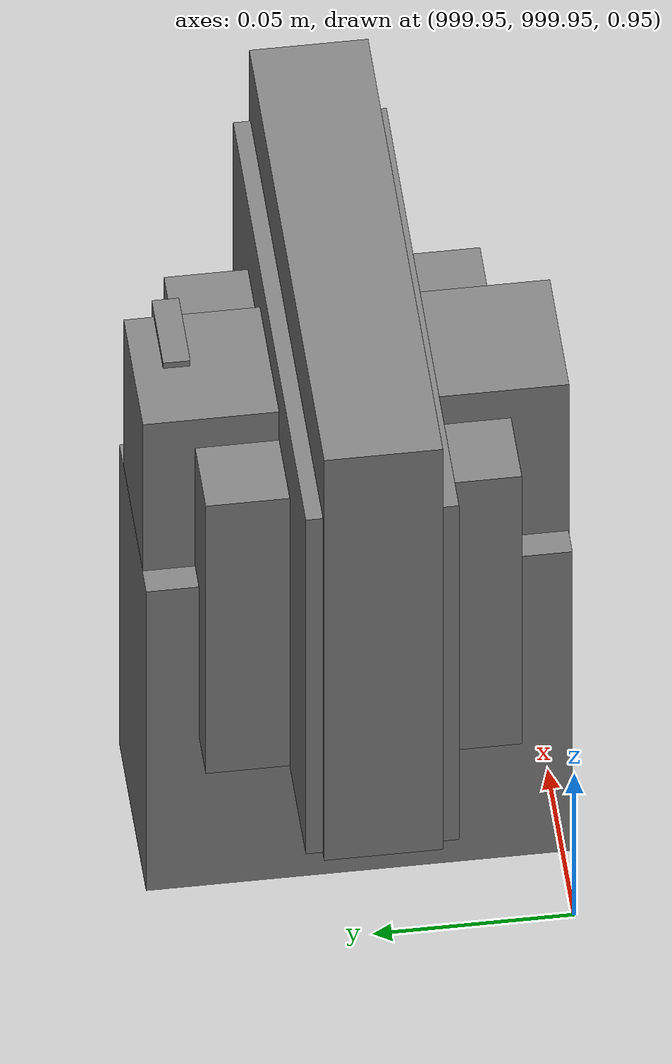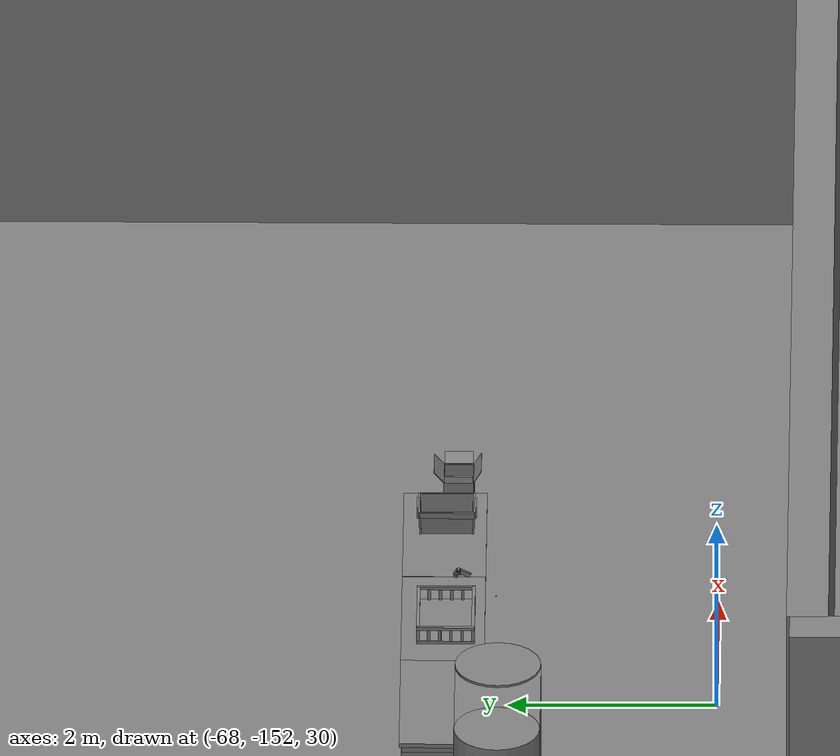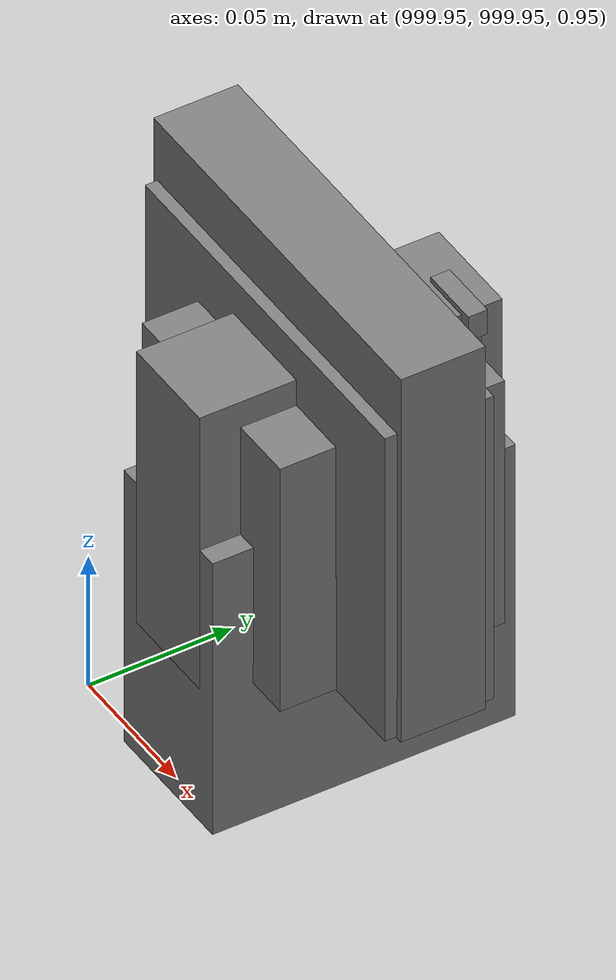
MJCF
<mujoco>
    <option gravity="0.000000000 0.000000000 -9.810000420" timestep="0.0049999999" integrator="implicitfast" density="1.225" viscosity="1.8000001e-05" noslip_iterations="10" iterations="100" sdf_iterations="50">
        <flag multiccd="disable"/>
    </option>
    <size memory="1000M"/>
    <compiler coordinate="local"/>
    <worldbody>
        <light cutoff="30" pos="0 1 1" dir="0 -1 -2"/>
        <light cutoff="30" pos="0 -1 1" dir="0 1 -2"/>
        <body pos="1000.000000000 1000.000000000 1.000000000" euler="0.000000000 0.000000000 180.000000000" name="openloong_gripper_2f85_fix_base_usda_battery_01">
            <geom contype="1" conaffinity="1" density="1000" type="box" material="" rgba="0.500000000 0.500000000 0.500000000 1.000000000" solimp="0.899999976 0.949999988 0.001000000" friction="1.000000000 0.005000000 0.000100000" solref="0.020000000 1.000000000" margin="0" condim="3" group="0" pos="-0.011123657 -0.041940309 0.101691343" quat="1.000000000 0.000000000 0.000000000 0.000000000" size="0.010800000 0.003375000 0.004725000" name="openloong_gripper_2f85_fix_base_usda_geom_54CB42CB_9DC4_40EE_BCFD_BC5AF397DA00"/>
            <geom contype="1" conaffinity="1" density="1000" type="box" material="" rgba="0.500000000 0.500000000 0.500000000 1.000000000" solimp="0.899999976 0.949999988 0.001000000" friction="1.000000000 0.005000000 0.000100000" solref="0.020000000 1.000000000" margin="0" condim="3" group="0" pos="-0.010876465 -0.044247437 0.047066893" quat="0.998702705 -0.050920475 0.000000000 0.000000000" size="0.009450001 0.002700000 0.024975000" name="openloong_gripper_2f85_fix_base_usda_geom_97BFB06C_C356_4838_AE4A_1D3FFBE1EEF2"/>
            <geom contype="1" conaffinity="1" density="1000" type="box" material="" rgba="0.500000000 0.500000000 0.500000000 1.000000000" solimp="0.899999976 0.949999988 0.001000000" friction="1.000000000 0.005000000 0.000100000" solref="0.020000000 1.000000000" margin="0" condim="3" group="0" pos="-0.001235962 -0.000659180 0.047381196" quat="1.000000000 0.000000000 0.000000000 0.000000000" size="0.039420001 0.039150000 0.047250003" name="openloong_gripper_2f85_fix_base_usda_geom_69D0DEEE_7163_4605_9F02_4A739E0891E3"/>
            <geom contype="1" conaffinity="1" density="1000" type="box" material="" rgba="0.500000000 0.500000000 0.500000000 1.000000000" solimp="0.899999976 0.949999988 0.001000000" friction="1.000000000 0.005000000 0.000100000" solref="0.020000000 1.000000000" margin="0" condim="3" group="0" pos="-0.010876465 -0.039138794 0.009851727" quat="1.000000000 0.000000000 0.000000000 0.000000000" size="0.009450001 0.010800000 0.013500000" name="openloong_gripper_2f85_fix_base_usda_geom_5C13ADBF_37C6_4B8F_91C0_9A7D85766F2E"/>
            <geom contype="1" conaffinity="1" density="1000" type="box" material="" rgba="0.500000000 0.500000000 0.500000000 1.000000000" solimp="0.899999976 0.949999988 0.001000000" friction="1.000000000 0.005000000 0.000100000" solref="0.020000000 1.000000000" margin="0" condim="3" group="0" pos="-0.010876465 -0.041528322 0.071508206" quat="1.000000000 0.000000000 0.000000000 0.000000000" size="0.009450001 0.002700000 0.027000001" name="openloong_gripper_2f85_fix_base_usda_geom_F3CD00F3_5336_48AC_9C38_28488DA69F7D"/>
            <freejoint name="openloong_gripper_2f85_fix_base_usda_battery_01_joint"/>
            <site size="0.005000000 0.005000000 0.005000000" rgba="0.500000000 0.500000000 0.500000000 1.000000000" pos="0.000000000 0.000000000 0.000000000" quat="0.999961913 0.008726500 0.000000000 0.000000000" group="0" type="sphere" name="openloong_gripper_2f85_fix_base_usda_battery_01site"/>
        </body>
        <body pos="-66.194061279 -149.056457520 31.165418625" euler="108.029518127 -2.319424152 -2.286916494" mocap="true" name="spotlight4_SpotLight"/>
        <body pos="-66.225158691 -149.778198242 31.162021637" euler="-102.525398254 -53.104270935 144.765655518" mocap="true" name="spotlight3_SpotLight"/>
        <body pos="1000.000000000 1000.000000000 1.000000000" euler="0.000000000 0.000000000 180.000000000" name="openloong_gripper_2f85_fix_base_usda_cpu_fan">
            <geom contype="1" conaffinity="1" density="1000" type="box" material="" rgba="0.500000000 0.500000000 0.500000000 1.000000000" solimp="0.899999976 0.949999988 0.001000000" friction="1.000000000 0.005000000 0.000100000" solref="0.020000000 1.000000000" margin="0" condim="3" group="0" pos="0.000000000 0.000000000 0.070034981" quat="0.000000000 0.000000000 0.000000000 1.000000000" size="0.070700005 0.014699999 0.070700005" name="openloong_gripper_2f85_fix_base_usda_geom_BC9F5F1E_9BBD_4314_A009_7CB6438071D9"/>
            <freejoint name="openloong_gripper_2f85_fix_base_usda_cpu_fan_joint"/>
            <site size="0.005000000 0.005000000 0.005000000" rgba="0.500000000 0.500000000 0.500000000 1.000000000" pos="0.000000000 0.000000000 0.000000000" quat="0.999961913 0.008726535 0.000000000 0.000000000" group="0" type="sphere" name="openloong_gripper_2f85_fix_base_usda_cpu_fancsite"/>
        </body>
        <body pos="1000.000000000 1000.000000000 1.000000000" euler="0.000000000 0.000000000 180.000000000" name="openloong_gripper_2f85_fix_base_usda_wifi_box">
            <geom contype="1" conaffinity="1" density="1000" type="box" material="" rgba="0.500000000 0.500000000 0.500000000 1.000000000" solimp="0.899999976 0.949999988 0.001000000" friction="1.000000000 0.005000000 0.000100000" solref="0.020000000 1.000000000" margin="0" condim="3" group="0" pos="0.000000000 0.000000000 0.058978677" quat="0.000000000 0.000000047 0.000000000 1.000000000" size="0.068499997 0.018999999 0.059000000" name="openloong_gripper_2f85_fix_base_usda_geom_F1732AB4_2EFC_4503_A23D_57DE598D0CE3"/>
            <freejoint name="openloong_gripper_2f85_fix_base_usda_wifi_box_joint"/>
            <site size="0.005000000 0.005000000 0.005000000" rgba="0.500000000 0.500000000 0.500000000 1.000000000" pos="0.000000000 0.000000000 0.000000000" quat="0.999961913 0.008726500 0.000000000 0.000000000" group="0" type="sphere" name="openloong_gripper_2f85_fix_base_usda_wifi_boxsite"/>
        </body>
        <body pos="1000.000000000 1000.000000000 1.000000000" euler="0.000011953 0.000005123 -179.999984741" name="openloong_gripper_2f85_fix_base_usda_intel_box">
            <geom contype="1" conaffinity="1" density="1000" type="box" material="" rgba="0.500000000 0.500000000 0.500000000 1.000000000" solimp="0.899999976 0.949999988 0.001000000" friction="1.000000000 0.005000000 0.000100000" solref="0.020000000 1.000000000" margin="0" condim="3" group="0" pos="0.000000000 -0.000067139 0.000082284" quat="0.707106709 0.000000225 0.000000253 0.707106650" size="0.052800003 0.025300000 0.052800003" name="openloong_gripper_2f85_fix_base_usda_geom_FC1EC99E_C5E5_421F_B020_AF0393EC94E4"/>
            <freejoint name="openloong_gripper_2f85_fix_base_usda_intel_box_joint"/>
            <site size="0.005000000 0.005000000 0.005000000" rgba="0.500000000 0.500000000 0.500000000 1.000000000" pos="0.000000000 0.000000000 0.000000000" quat="0.999961913 0.008726500 0.000000000 0.000000000" group="0" type="sphere" name="openloong_gripper_2f85_fix_base_usda_intel_boxsite"/>
        </body>
        <body pos="1000.000000000 999.999938965 1.000000000" euler="0.000000000 0.000000000 180.000000000" name="openloong_gripper_2f85_fix_base_usda_intelcore_i5">
            <geom contype="1" conaffinity="1" density="1000" type="box" material="" rgba="0.500000000 0.500000000 0.500000000 1.000000000" solimp="0.899999976 0.949999988 0.001000000" friction="1.000000000 0.005000000 0.000100000" solref="0.020000000 1.000000000" margin="0" condim="3" group="0" pos="0.000000000 0.000000000 0.051722717" quat="0.707106709 0.000000000 0.000000000 -0.707106769" size="0.052800000 0.018080002 0.052800000" name="openloong_gripper_2f85_fix_base_usda_geom_8005446C_9260_4FF9_A590_E31766C022FA"/>
            <freejoint name="openloong_gripper_2f85_fix_base_usda_intelcore_i5_joint"/>
            <site size="0.005000000 0.005000000 0.005000000" rgba="0.500000000 0.500000000 0.500000000 1.000000000" pos="0.000000000 0.000000000 0.000000000" quat="0.999961913 0.008726534 0.000000000 0.000000000" group="0" type="sphere" name="openloong_gripper_2f85_fix_base_usda_intelcore_i5site"/>
        </body>
        <body pos="-66.192222595 -149.393035889 31.162345886" euler="66.333267212 -58.086212158 131.021316528" mocap="true" name="spotlight2_SpotLight"/>
        <body pos="-64.866622925 -149.383972168 30.183746338" euler="89.999984741 89.999946594 0.000000000" name="openloong_gripper_2f85_fix_base_usda_bluebox_01">
            <geom contype="1" conaffinity="1" density="1000" type="box" material="" rgba="0.500000000 0.500000000 0.500000000 1.000000000" solimp="0.899999976 0.949999988 0.001000000" friction="1.000000000 0.005000000 0.000100000" solref="0.020000000 1.000000000" margin="0" condim="3" group="0" pos="0.276580811 0.187225342 0.000068665" quat="0.707106948 0.000077471 0.707106352 0.000077486" size="0.100000001 0.057999998 0.010000000" name="openloong_gripper_2f85_fix_base_usda_geom_34A57286_A619_4BF1_BBD9_7719E1853731"/>
            <geom contype="1" conaffinity="1" density="1000" type="box" material="" rgba="0.500000000 0.500000000 0.500000000 1.000000000" solimp="0.899999976 0.949999988 0.001000000" friction="1.000000000 0.005000000 0.000100000" solref="0.020000000 1.000000000" margin="0" condim="3" group="0" pos="0.000000000 0.002883911 0.000000000" quat="0.999999881 0.000000000 0.000000000 0.000000000" size="0.254000008 0.003000000 0.172000006" name="openloong_gripper_2f85_fix_base_usda_geom_65F4C748_1CD1_4695_9E37_E3C05B6911A2"/>
            <geom contype="1" conaffinity="1" density="1000" type="box" material="" rgba="0.500000000 0.500000000 0.500000000 1.000000000" solimp="0.899999976 0.949999988 0.001000000" friction="1.000000000 0.005000000 0.000100000" solref="0.020000000 1.000000000" margin="0" condim="3" group="0" pos="0.000000000 0.124874115 0.173484802" quat="0.999796331 0.020176515 -0.000000015 0.000000030" size="0.259999990 0.119999997 0.007000000" name="openloong_gripper_2f85_fix_base_usda_geom_7ADA07AF_4620_4821_9319_5CD2F93673FB"/>
            <geom contype="1" conaffinity="1" density="1000" type="box" material="" rgba="0.500000000 0.500000000 0.500000000 1.000000000" solimp="0.899999976 0.949999988 0.001000000" friction="1.000000000 0.005000000 0.000100000" solref="0.020000000 1.000000000" margin="0" condim="3" group="0" pos="0.000000000 0.124874115 -0.173469543" quat="0.999796331 -0.020176545 -0.000000015 0.000000000" size="0.259999990 0.119999997 0.007000000" name="openloong_gripper_2f85_fix_base_usda_geom_B6F34AC7_C1DC_40A6_97DE_7439084BACBF"/>
            <geom contype="1" conaffinity="1" density="1000" type="box" material="" rgba="0.500000000 0.500000000 0.500000000 1.000000000" solimp="0.899999976 0.949999988 0.001000000" friction="1.000000000 0.005000000 0.000100000" solref="0.020000000 1.000000000" margin="0" condim="3" group="0" pos="0.000000000 0.214008331 0.188980103" quat="0.999912977 0.013176724 0.000000015 0.000000000" size="0.259999990 0.029999999 0.012500000" name="openloong_gripper_2f85_fix_base_usda_geom_FA0E6116_5505_45DB_9E21_EF7A8BCCC8C3"/>
            <geom contype="1" conaffinity="1" density="1000" type="box" material="" rgba="0.500000000 0.500000000 0.500000000 1.000000000" solimp="0.899999976 0.949999988 0.001000000" friction="1.000000000 0.005000000 0.000100000" solref="0.020000000 1.000000000" margin="0" condim="3" group="0" pos="-0.258361816 0.125289917 0.001876831" quat="0.702796936 -0.020792112 0.710783124 0.020769298" size="0.189999998 0.119999997 0.009000000" name="openloong_gripper_2f85_fix_base_usda_geom_4D87B99D_2E5E_440B_A16B_45485DE3B99C"/>
            <geom contype="1" conaffinity="1" density="1000" type="box" material="" rgba="0.500000000 0.500000000 0.500000000 1.000000000" solimp="0.899999976 0.949999988 0.001000000" friction="1.000000000 0.005000000 0.000100000" solref="0.020000000 1.000000000" margin="0" condim="3" group="0" pos="0.000000000 0.214008331 -0.188980103" quat="0.999912977 -0.013176769 0.000000030 0.000000015" size="0.259999990 0.029999999 0.012500000" name="openloong_gripper_2f85_fix_base_usda_geom_B00ADF94_B3F7_40C9_95EF_6664FED1C59A"/>
            <geom contype="1" conaffinity="1" density="1000" type="box" material="" rgba="0.500000000 0.500000000 0.500000000 1.000000000" solimp="0.899999976 0.949999988 0.001000000" friction="1.000000000 0.005000000 0.000100000" solref="0.020000000 1.000000000" margin="0" condim="3" group="0" pos="-0.276611328 0.187225342 0.000068665" quat="0.707106650 0.000077441 0.707106709 0.000077456" size="0.100000001 0.057999998 0.010000000" name="openloong_gripper_2f85_fix_base_usda_geom_58C1394E_9946_4C1B_8C0F_B3CBFA5A7D62"/>
            <geom contype="1" conaffinity="1" density="1000" type="box" material="" rgba="0.500000000 0.500000000 0.500000000 1.000000000" solimp="0.899999976 0.949999988 0.001000000" friction="1.000000000 0.005000000 0.000100000" solref="0.020000000 1.000000000" margin="0" condim="3" group="0" pos="0.258331299 0.125289917 0.001876831" quat="0.702851415 0.018856421 0.710823774 -0.019329369" size="0.189999998 0.119999997 0.009000000" name="openloong_gripper_2f85_fix_base_usda_geom_368089FF_8DAD_44D4_BBCC_4C694F2E2BE5"/>
            <freejoint name="openloong_gripper_2f85_fix_base_usda_bluebox_01_joint"/>
            <site size="0.005000000 0.005000000 0.005000000" rgba="0.500000000 0.500000000 0.500000000 1.000000000" pos="0.000000000 0.000000000 0.000000000" quat="0.999961913 0.008726534 0.000000000 0.000000000" group="0" type="sphere" name="openloong_gripper_2f85_fix_base_usda_bluebox_01site"/>
        </body>
        <body pos="-64.496299744 -149.491867065 30.235729218" euler="0.000000000 0.000000000 89.999946594" name="openloong_gripper_2f85_fix_base_usda_cardboardbox_01">
            <geom contype="1" conaffinity="1" density="1000" type="box" material="" rgba="0.500000000 0.500000000 0.500000000 1.000000000" solimp="0.899999976 0.949999988 0.001000000" friction="1.000000000 0.005000000 0.000100000" solref="0.020000000 1.000000000" margin="0" condim="3" group="0" pos="-0.003166199 -0.004086494 0.005052090" quat="1.000000000 0.000000000 0.000000000 0.000000000" size="0.142499998 0.177500010 0.005000000" name="openloong_gripper_2f85_fix_base_usda_geom_F4AD22AE_B42C_44A0_BE3C_B41D8959196E"/>
            <geom contype="1" conaffinity="1" density="1000" type="box" material="" rgba="0.500000000 0.500000000 0.500000000 1.000000000" solimp="0.899999976 0.949999988 0.001000000" friction="1.000000000 0.005000000 0.000100000" solref="0.020000000 1.000000000" margin="0" condim="3" group="0" pos="-0.003166199 0.170316696 0.150570869" quat="1.000000000 0.000000000 0.000000000 0.000000000" size="0.142499998 0.005000000 0.149999991" name="openloong_gripper_2f85_fix_base_usda_geom_88D2F356_BC5D_4508_9437_A295FBBDD136"/>
            <geom contype="1" conaffinity="1" density="1000" type="box" material="" rgba="0.500000000 0.500000000 0.500000000 1.000000000" solimp="0.899999976 0.949999988 0.001000000" friction="1.000000000 0.005000000 0.000100000" solref="0.020000000 1.000000000" margin="0" condim="3" group="0" pos="-0.147399902 -0.005307198 0.150570869" quat="1.000000000 0.000000000 0.000000000 0.000000000" size="0.005000000 0.177500010 0.149999991" name="openloong_gripper_2f85_fix_base_usda_geom_871AA61D_B6A4_4972_B991_75F4772BA774"/>
            <geom contype="1" conaffinity="1" density="1000" type="box" material="" rgba="0.500000000 0.500000000 0.500000000 1.000000000" solimp="0.899999976 0.949999988 0.001000000" friction="1.000000000 0.005000000 0.000100000" solref="0.020000000 1.000000000" margin="0" condim="3" group="0" pos="0.140275955 -0.005307198 0.150570869" quat="1.000000000 0.000000000 0.000000000 0.000000000" size="0.005000000 0.177500010 0.149999991" name="openloong_gripper_2f85_fix_base_usda_geom_7D242D55_9FD9_4732_A276_993FFD77BB8D"/>
            <geom contype="1" conaffinity="1" density="1000" type="box" material="" rgba="0.500000000 0.500000000 0.500000000 1.000000000" solimp="0.899999976 0.949999988 0.001000000" friction="1.000000000 0.005000000 0.000100000" solref="0.020000000 1.000000000" margin="0" condim="3" group="0" pos="-0.003166199 -0.181550980 0.150570869" quat="1.000000000 0.000000000 0.000000000 0.000000000" size="0.142499998 0.005000000 0.149999991" name="openloong_gripper_2f85_fix_base_usda_geom_20F7BCE9_5685_4645_A917_E76A353258D8"/>
            <freejoint name="openloong_gripper_2f85_fix_base_usda_cardboardbox_01_joint"/>
            <site size="0.005000000 0.005000000 0.005000000" rgba="0.500000000 0.500000000 0.500000000 1.000000000" pos="0.000000000 0.000000000 0.000000000" quat="0.999961913 0.008726535 0.000000000 0.000000000" group="0" type="sphere" name="openloong_gripper_2f85_fix_base_usda_site_0E6B9862_49B2_4959_95B8_F850EC614BD8"/>
            <body pos="0.139160156 -0.004048347 0.301930904" euler="-179.999954224 49.383502960 179.999954224" name="openloong_gripper_2f85_fix_base_usda_A1_006">
                <geom contype="1" conaffinity="1" density="1000" type="box" material="" rgba="0.500000000 0.500000000 0.500000000 1.000000000" solimp="0.899999976 0.949999988 0.001000000" friction="1.000000000 0.005000000 0.000100000" solref="0.020000000 1.000000000" margin="0" condim="3" group="0" pos="-0.071587563 0.000009537 0.001745224" quat="0.999999881 0.000000000 0.000000000 0.000000000" size="0.071249999 0.179999992 0.002500000" name="openloong_gripper_2f85_fix_base_usda_geom_E70E6197_57E6_4910_8A20_B0B7B2B0DED1"/>
                <joint armature="0" stiffness="0.07" damping="0.0099999998" axis="0.000000 1.000000 0.000000" type="hinge" name="openloong_gripper_2f85_fix_base_usda_A1_006"/>
            </body>
            <body pos="-0.145902634 -0.004086494 0.301938057" euler="-180.000000000 -60.000011444 -180.000000000" name="openloong_gripper_2f85_fix_base_usda_A2_006">
                <geom contype="1" conaffinity="1" density="1000" type="box" material="" rgba="0.500000000 0.500000000 0.500000000 1.000000000" solimp="0.899999976 0.949999988 0.001000000" friction="1.000000000 0.005000000 0.000100000" solref="0.020000000 1.000000000" margin="0" condim="3" group="0" pos="0.071268082 0.000009537 0.002717972" quat="0.000002921 0.000000000 -0.000000030 0.999999881" size="0.071249999 0.179999992 0.002500000" name="openloong_gripper_2f85_fix_base_usda_geom_A9DB3F1A_0AE1_48FE_8868_97125FE397F2"/>
                <joint armature="0" stiffness="0.07" damping="0.0099999998" axis="0.000000 1.000000 0.000000" type="hinge" name="openloong_gripper_2f85_fix_base_usda_A2_006"/>
            </body>
            <body pos="-0.003385544 0.175991058 0.301930904" euler="-125.858116150 -0.000004561 0.000002331" name="openloong_gripper_2f85_fix_base_usda_B2_006">
                <geom contype="1" conaffinity="1" density="1000" type="box" material="" rgba="0.500000000 0.500000000 0.500000000 1.000000000" solimp="0.899999976 0.949999988 0.001000000" friction="1.000000000 0.005000000 0.000100000" solref="0.020000000 1.000000000" margin="0" condim="3" group="0" pos="0.000009537 -0.070939064 -0.002470016" quat="0.999614120 0.027776197 -0.000000015 0.000000030" size="0.137500003 0.064999998 0.005000000" name="openloong_gripper_2f85_fix_base_usda_geom_503D89B6_71D0_4D5E_8DA0_51D4DFEC951A"/>
                <joint armature="0" stiffness="0.07" damping="0.0099999998" axis="1.000000 0.000000 0.000000" type="hinge" name="openloong_gripper_2f85_fix_base_usda_B2_006"/>
            </body>
            <body pos="-0.003385544 -0.184140205 0.301938057" euler="147.805557251 0.000000000 0.000000000" name="openloong_gripper_2f85_fix_base_usda_B1_006">
                <geom contype="1" conaffinity="1" density="1000" type="box" material="" rgba="0.500000000 0.500000000 0.500000000 1.000000000" solimp="0.899999976 0.949999988 0.001000000" friction="1.000000000 0.005000000 0.000100000" solref="0.020000000 1.000000000" margin="0" condim="3" group="0" pos="-0.000028610 0.070202351 -0.002703667" quat="0.999614179 -0.027776167 0.000000000 0.000000000" size="0.137500003 0.064999998 0.005000000" name="openloong_gripper_2f85_fix_base_usda_geom_74A79556_2B4C_448C_8922_D252C7752D76"/>
                <joint armature="0" stiffness="0.07" damping="0.0099999998" axis="1.000000 0.000000 0.000000" type="hinge" name="openloong_gripper_2f85_fix_base_usda_B1_006"/>
            </body>
        </body>
        <body pos="-65.882858276 -149.481979370 30.229999542" euler="-64.487716675 0.000000000 0.000000000" name="openloong_gripper_2f85_fix_base_usda_Barcode">
            <geom contype="1" conaffinity="1" density="1000" type="box" material="" rgba="0.500000000 0.500000000 0.500000000 1.000000000" solimp="0.899999976 0.949999988 0.001000000" friction="1.000000000 0.005000000 0.000100000" solref="0.020000000 1.000000000" margin="0" condim="3" group="0" pos="0.000000000 0.013038635 0.001419067" quat="0.000000000 0.000000000 0.000000000 1.000000119" size="0.034000002 0.010000000 0.017999999" name="openloong_gripper_2f85_fix_base_usda_geom_E7E3FCEF_D0C3_44CE_BB31_31EA738FB926"/>
            <geom contype="1" conaffinity="1" density="1000" type="box" material="" rgba="0.500000000 0.500000000 0.500000000 1.000000000" solimp="0.899999976 0.949999988 0.001000000" friction="1.000000000 0.005000000 0.000100000" solref="0.020000000 1.000000000" margin="0" condim="3" group="0" pos="0.000000000 -0.035301208 -0.007095337" quat="0.000000000 0.000000000 -0.043619365 0.999048233" size="0.028999999 0.010000000 0.020000000" name="openloong_gripper_2f85_fix_base_usda_geom_DD505EE5_CDDA_44E0_8F23_28A1FA5FC0BD"/>
            <geom contype="1" conaffinity="1" density="1000" type="box" material="" rgba="0.500000000 0.500000000 0.500000000 1.000000000" solimp="0.899999976 0.949999988 0.001000000" friction="1.000000000 0.005000000 0.000100000" solref="0.020000000 1.000000000" margin="0" condim="3" group="0" pos="0.000000000 -0.043411255 -0.011749268" quat="0.922262907 0.386563420 0.000000000 0.000000000" size="0.026000001 0.010000000 0.020000000" name="openloong_gripper_2f85_fix_base_usda_geom_A06F9E80_47B8_4910_9D71_3FC25EA253A9"/>
            <geom contype="1" conaffinity="1" density="1000" type="box" material="" rgba="0.500000000 0.500000000 0.500000000 1.000000000" solimp="0.899999976 0.949999988 0.001000000" friction="1.000000000 0.005000000 0.000100000" solref="0.020000000 1.000000000" margin="0" condim="3" group="0" pos="0.000000000 -0.016967773 -0.031860352" quat="0.000000000 0.000000000 0.000000000 1.000000119" size="0.008000000 0.010000000 0.013000000" name="openloong_gripper_2f85_fix_base_usda_geom_F589B86F_29B1_4E66_B9E3_75D1E34CC815"/>
            <geom contype="1" conaffinity="1" density="1000" type="box" material="" rgba="0.500000000 0.500000000 0.500000000 1.000000000" solimp="0.899999976 0.949999988 0.001000000" friction="1.000000000 0.005000000 0.000100000" solref="0.020000000 1.000000000" margin="0" condim="3" group="0" pos="0.000000000 -0.001869202 0.000312805" quat="0.953716993 0.300705761 0.000000000 0.000000000" size="0.032000002 0.010000000 0.018999999" name="openloong_gripper_2f85_fix_base_usda_geom_5549A115_F05E_43F0_9CF5_16BF082962B6"/>
            <geom contype="1" conaffinity="1" density="1000" type="box" material="" rgba="0.500000000 0.500000000 0.500000000 1.000000000" solimp="0.899999976 0.949999988 0.001000000" friction="1.000000000 0.005000000 0.000100000" solref="0.020000000 1.000000000" margin="0" condim="3" group="0" pos="0.000000000 -0.019531250 -0.003173828" quat="0.953716993 0.300705761 0.000000000 0.000000000" size="0.030999999 0.010000000 0.020000000" name="openloong_gripper_2f85_fix_base_usda_geom_372DF156_5387_4314_8F7E_FA6F78BC2D29"/>
            <geom contype="1" conaffinity="1" density="1000" type="box" material="" rgba="0.500000000 0.500000000 0.500000000 1.000000000" solimp="0.899999976 0.949999988 0.001000000" friction="1.000000000 0.005000000 0.000100000" solref="0.020000000 1.000000000" margin="0" condim="3" group="0" pos="0.000000000 -0.035301208 -0.007095337" quat="0.953716993 0.300705761 0.000000000 0.000000000" size="0.028999999 0.010000000 0.020000000" name="openloong_gripper_2f85_fix_base_usda_geom_C9D708D8_9AF3_4D83_98C7_E895496C2959"/>
            <geom contype="1" conaffinity="1" density="1000" type="box" material="" rgba="0.500000000 0.500000000 0.500000000 1.000000000" solimp="0.899999976 0.949999988 0.001000000" friction="1.000000000 0.005000000 0.000100000" solref="0.020000000 1.000000000" margin="0" condim="3" group="0" pos="0.000000000 -0.042617798 -0.071121216" quat="0.000000000 0.000000000 0.000000000 1.000000119" size="0.013000000 0.021000000 0.059999999" name="openloong_gripper_2f85_fix_base_usda_geom_D952134A_4D10_4F02_87CE_7F44E383F042"/>
            <freejoint name="openloong_gripper_2f85_fix_base_usda_Barcode_joint"/>
            <site size="0.005000000 0.005000000 0.005000000" rgba="0.500000000 0.500000000 0.500000000 1.000000000" pos="0.000000000 0.000000000 0.000000000" quat="1.000000000 0.000000000 0.000000000 0.000000000" group="0" type="sphere" name="openloong_gripper_2f85_fix_base_usda_Barcode_site"/>
        </body>
        <body pos="-66.745018005 -149.392349243 30.184000015" euler="0.000000000 0.000000000 89.999946594" name="[22331266781280]_Basket_01">
            <geom contype="1" conaffinity="1" density="1000" type="box" material="" rgba="0.500000000 0.500000000 0.500000000 1.000000000" solimp="0.899999976 0.949999988 0.001000000" friction="1.000000000 0.005000000 0.000100000" solref="0.020000000 1.000000000" margin="0" condim="3" group="0" pos="-0.052425385 0.389207840 0.089787483" quat="0.707107008 0.000000000 0.000000000 0.707106411" size="0.014249999 0.014249999 0.059999999" name="[22331266781280]_geom_76860122_62FD_464F_B81E_44BF3CB3D900"/>
            <geom contype="1" conaffinity="1" density="1000" type="box" material="" rgba="0.500000000 0.500000000 0.500000000 1.000000000" solimp="0.899999976 0.949999988 0.001000000" friction="1.000000000 0.005000000 0.000100000" solref="0.020000000 1.000000000" margin="0" condim="3" group="0" pos="0.264015198 -0.133043289 0.089787483" quat="0.707107008 0.000000000 0.000000000 0.707106411" size="0.014249999 0.014249999 0.059999999" name="[22331266781280]_geom_D9D4438D_6B94_4373_9706_E10A7378D41B"/>
            <geom contype="1" conaffinity="1" density="1000" type="box" material="" rgba="0.500000000 0.500000000 0.500000000 1.000000000" solimp="0.899999976 0.949999988 0.001000000" friction="1.000000000 0.005000000 0.000100000" solref="0.020000000 1.000000000" margin="0" condim="3" group="0" pos="-0.264015198 -0.265548706 0.089793205" quat="0.707107008 0.000000000 0.000000000 0.707106411" size="0.014249999 0.014249999 0.059999999" name="[22331266781280]_geom_078E5F1D_D61C_4D38_B8AA_E32EC173CF40"/>
            <geom contype="1" conaffinity="1" density="1000" type="box" material="" rgba="0.500000000 0.500000000 0.500000000 1.000000000" solimp="0.899999976 0.949999988 0.001000000" friction="1.000000000 0.005000000 0.000100000" solref="0.020000000 1.000000000" margin="0" condim="3" group="0" pos="-0.160263062 -0.389322281 0.089793205" quat="0.707107008 0.000000000 0.000000000 0.707106411" size="0.014249999 0.014249999 0.059999999" name="[22331266781280]_geom_126D0324_4D32_4E2D_9BE9_A4440155BF96"/>
            <geom contype="1" conaffinity="1" density="1000" type="box" material="" rgba="0.500000000 0.500000000 0.500000000 1.000000000" solimp="0.899999976 0.949999988 0.001000000" friction="1.000000000 0.005000000 0.000100000" solref="0.020000000 1.000000000" margin="0" condim="3" group="0" pos="0.162265778 -0.389322281 0.089787483" quat="0.707107008 0.000000000 0.000000000 0.707106411" size="0.014249999 0.014249999 0.059999999" name="[22331266781280]_geom_C4D7F9E9_8952_490B_A9DF_1C26C30993E6"/>
            <geom contype="1" conaffinity="1" density="1000" type="box" material="" rgba="0.500000000 0.500000000 0.500000000 1.000000000" solimp="0.899999976 0.949999988 0.001000000" friction="1.000000000 0.005000000 0.000100000" solref="0.020000000 1.000000000" margin="0" condim="3" group="0" pos="0.264015198 0.389207840 0.089787483" quat="0.707107008 0.000000000 0.000000000 0.707106411" size="0.014249999 0.014249999 0.059999999" name="[22331266781280]_geom_C5941A5F_6532_4A79_BFEF_62B6DE43AC10"/>
            <geom contype="1" conaffinity="1" density="1000" type="box" material="" rgba="0.500000000 0.500000000 0.500000000 1.000000000" solimp="0.899999976 0.949999988 0.001000000" friction="1.000000000 0.005000000 0.000100000" solref="0.020000000 1.000000000" margin="0" condim="3" group="0" pos="-0.264015198 -0.133043289 0.089793205" quat="0.707107008 0.000000000 0.000000000 0.707106411" size="0.014249999 0.014249999 0.059999999" name="[22331266781280]_geom_3FB09CF3_07C0_4758_8370_783874A16E6C"/>
            <geom contype="1" conaffinity="1" density="1000" type="box" material="" rgba="0.500000000 0.500000000 0.500000000 1.000000000" solimp="0.899999976 0.949999988 0.001000000" friction="1.000000000 0.005000000 0.000100000" solref="0.020000000 1.000000000" margin="0" condim="3" group="0" pos="-0.264026642 0.269256592 0.089793205" quat="0.707107008 0.000000000 0.000000000 0.707106411" size="0.014249999 0.014249999 0.059999999" name="[22331266781280]_geom_4CB59A2B_EBD4_4D50_B00A_72675A188C28"/>
            <geom contype="1" conaffinity="1" density="1000" type="box" material="" rgba="0.500000000 0.500000000 0.500000000 1.000000000" solimp="0.899999976 0.949999988 0.001000000" friction="1.000000000 0.005000000 0.000100000" solref="0.020000000 1.000000000" margin="0" condim="3" group="0" pos="0.054462433 0.389207840 0.089787483" quat="0.707107008 0.000000000 0.000000000 0.707106411" size="0.014249999 0.014249999 0.059999999" name="[22331266781280]_geom_B9A955A7_1F9E_46C3_A82C_1BF423EA5469"/>
            <geom contype="1" conaffinity="1" density="1000" type="box" material="" rgba="0.500000000 0.500000000 0.500000000 1.000000000" solimp="0.899999976 0.949999988 0.001000000" friction="1.000000000 0.005000000 0.000100000" solref="0.020000000 1.000000000" margin="0" condim="3" group="0" pos="0.054462433 -0.389322281 0.089787483" quat="0.707107008 0.000000000 0.000000000 0.707106411" size="0.014249999 0.014249999 0.059999999" name="[22331266781280]_geom_AECDEB34_5A0B_4252_9282_3AAA57D95E1F"/>
            <geom contype="1" conaffinity="1" density="1000" type="box" material="" rgba="0.500000000 0.500000000 0.500000000 1.000000000" solimp="0.899999976 0.949999988 0.001000000" friction="1.000000000 0.005000000 0.000100000" solref="0.020000000 1.000000000" margin="0" condim="3" group="0" pos="0.264015198 0.269256592 0.089793205" quat="0.707107008 0.000000000 0.000000000 0.707106411" size="0.014249999 0.014249999 0.059999999" name="[22331266781280]_geom_19AB676F_9B5B_4D69_8110_2838F9FE994C"/>
            <geom contype="1" conaffinity="1" density="1000" type="box" material="" rgba="0.500000000 0.500000000 0.500000000 1.000000000" solimp="0.899999976 0.949999988 0.001000000" friction="1.000000000 0.005000000 0.000100000" solref="0.020000000 1.000000000" margin="0" condim="3" group="0" pos="0.264015198 -0.389322281 0.089787483" quat="0.707107008 0.000000000 0.000000000 0.707106411" size="0.014249999 0.014249999 0.059999999" name="[22331266781280]_geom_D50B9A37_A9E3_4B2F_A4F5_F4611500F39A"/>
            <geom contype="1" conaffinity="1" density="1000" type="box" material="" rgba="0.500000000 0.500000000 0.500000000 1.000000000" solimp="0.899999976 0.949999988 0.001000000" friction="1.000000000 0.005000000 0.000100000" solref="0.020000000 1.000000000" margin="0" condim="3" group="0" pos="0.000000000 0.000000000 0.015998840" quat="0.707107008 0.000000000 0.000000000 0.707106411" size="0.403499991 0.279000014 0.015750000" name="[22331266781280]_geom_33FDEF65_791A_4182_AED2_C27B18B7B75D"/>
            <geom contype="1" conaffinity="1" density="1000" type="box" material="" rgba="0.500000000 0.500000000 0.500000000 1.000000000" solimp="0.899999976 0.949999988 0.001000000" friction="1.000000000 0.005000000 0.000100000" solref="0.020000000 1.000000000" margin="0" condim="3" group="0" pos="0.000000000 -0.389476776 0.163619041" quat="0.707107008 0.000000000 0.000000000 0.707106411" size="0.015000000 0.277500004 0.015750000" name="[22331266781280]_geom_71425DAE_A4D4_462A_8825_E2DE69FEE950"/>
            <geom contype="1" conaffinity="1" density="1000" type="box" material="" rgba="0.500000000 0.500000000 0.500000000 1.000000000" solimp="0.899999976 0.949999988 0.001000000" friction="1.000000000 0.005000000 0.000100000" solref="0.020000000 1.000000000" margin="0" condim="3" group="0" pos="0.162265778 0.389207840 0.089787483" quat="0.707107008 0.000000000 0.000000000 0.707106411" size="0.014249999 0.014249999 0.059999999" name="[22331266781280]_geom_8AF75D87_0C2A_4EF2_93B4_86D5484F0ECD"/>
            <geom contype="1" conaffinity="1" density="1000" type="box" material="" rgba="0.500000000 0.500000000 0.500000000 1.000000000" solimp="0.899999976 0.949999988 0.001000000" friction="1.000000000 0.005000000 0.000100000" solref="0.020000000 1.000000000" margin="0" condim="3" group="0" pos="0.000000000 0.389471054 0.163619041" quat="0.707107008 0.000000000 0.000000000 0.707106411" size="0.015000000 0.277500004 0.015750000" name="[22331266781280]_geom_EA68849B_CF7E_4005_AB41_4931C7E427EF"/>
            <geom contype="1" conaffinity="1" density="1000" type="box" material="" rgba="0.500000000 0.500000000 0.500000000 1.000000000" solimp="0.899999976 0.949999988 0.001000000" friction="1.000000000 0.005000000 0.000100000" solref="0.020000000 1.000000000" margin="0" condim="3" group="0" pos="-0.263511658 0.000000000 0.163619041" quat="0.707107008 0.000000000 0.000000000 0.707106411" size="0.403499991 0.015000000 0.015750000" name="[22331266781280]_geom_FE27269F_1681_4D20_A734_665C133616CA"/>
            <geom contype="1" conaffinity="1" density="1000" type="box" material="" rgba="0.500000000 0.500000000 0.500000000 1.000000000" solimp="0.899999976 0.949999988 0.001000000" friction="1.000000000 0.005000000 0.000100000" solref="0.020000000 1.000000000" margin="0" condim="3" group="0" pos="-0.264015198 0.141334534 0.089793205" quat="0.707107008 0.000000000 0.000000000 0.707106411" size="0.014249999 0.014249999 0.059999999" name="[22331266781280]_geom_1FA7B3FD_5CB5_45DA_884E_21A7671156F9"/>
            <geom contype="1" conaffinity="1" density="1000" type="box" material="" rgba="0.500000000 0.500000000 0.500000000 1.000000000" solimp="0.899999976 0.949999988 0.001000000" friction="1.000000000 0.005000000 0.000100000" solref="0.020000000 1.000000000" margin="0" condim="3" group="0" pos="0.264015198 -0.265548706 0.089787483" quat="0.707107008 0.000000000 0.000000000 0.707106411" size="0.014249999 0.014249999 0.059999999" name="[22331266781280]_geom_F8AA56A0_E2E9_422E_8CD6_47B172013456"/>
            <geom contype="1" conaffinity="1" density="1000" type="box" material="" rgba="0.500000000 0.500000000 0.500000000 1.000000000" solimp="0.899999976 0.949999988 0.001000000" friction="1.000000000 0.005000000 0.000100000" solref="0.020000000 1.000000000" margin="0" condim="3" group="0" pos="-0.160263062 0.389207840 0.089787483" quat="0.707107008 0.000000000 0.000000000 0.707106411" size="0.014249999 0.014249999 0.059999999" name="[22331266781280]_geom_950912B5_787E_4567_86A0_48258E87074D"/>
            <geom contype="1" conaffinity="1" density="1000" type="box" material="" rgba="0.500000000 0.500000000 0.500000000 1.000000000" solimp="0.899999976 0.949999988 0.001000000" friction="1.000000000 0.005000000 0.000100000" solref="0.020000000 1.000000000" margin="0" condim="3" group="0" pos="-0.052425385 -0.389322281 0.089787483" quat="0.707107008 0.000000000 0.000000000 0.707106411" size="0.014249999 0.014249999 0.059999999" name="[22331266781280]_geom_B4F29D94_A607_4C1C_A723_50A170D23139"/>
            <geom contype="1" conaffinity="1" density="1000" type="box" material="" rgba="0.500000000 0.500000000 0.500000000 1.000000000" solimp="0.899999976 0.949999988 0.001000000" friction="1.000000000 0.005000000 0.000100000" solref="0.020000000 1.000000000" margin="0" condim="3" group="0" pos="-0.264026642 -0.389322281 0.089793205" quat="0.707107008 0.000000000 0.000000000 0.707106411" size="0.014249999 0.014249999 0.059999999" name="[22331266781280]_geom_29DA603D_F1E4_4D10_A0A9_087FE900CF74"/>
            <geom contype="1" conaffinity="1" density="1000" type="box" material="" rgba="0.500000000 0.500000000 0.500000000 1.000000000" solimp="0.899999976 0.949999988 0.001000000" friction="1.000000000 0.005000000 0.000100000" solref="0.020000000 1.000000000" margin="0" condim="3" group="0" pos="0.264015198 0.141334534 0.089787483" quat="0.707107008 0.000000000 0.000000000 0.707106411" size="0.014249999 0.014249999 0.059999999" name="[22331266781280]_geom_4AE36E20_FC34_46E7_AC84_E8CA07148198"/>
            <geom contype="1" conaffinity="1" density="1000" type="box" material="" rgba="0.500000000 0.500000000 0.500000000 1.000000000" solimp="0.899999976 0.949999988 0.001000000" friction="1.000000000 0.005000000 0.000100000" solref="0.020000000 1.000000000" margin="0" condim="3" group="0" pos="-0.264015198 0.389207840 0.089793205" quat="0.707107008 0.000000000 0.000000000 0.707106411" size="0.014249999 0.014249999 0.059999999" name="[22331266781280]_geom_CC25DEEC_0F42_406B_86F6_272A8B9EF50A"/>
            <geom contype="1" conaffinity="1" density="1000" type="box" material="" rgba="0.500000000 0.500000000 0.500000000 1.000000000" solimp="0.899999976 0.949999988 0.001000000" friction="1.000000000 0.005000000 0.000100000" solref="0.020000000 1.000000000" margin="0" condim="3" group="0" pos="0.264015198 0.004480362 0.089787483" quat="0.707107008 0.000000000 0.000000000 0.707106411" size="0.014249999 0.014249999 0.059999999" name="[22331266781280]_geom_47844EF2_D39D_405A_877C_F3B8730A5AC8"/>
            <geom contype="1" conaffinity="1" density="1000" type="box" material="" rgba="0.500000000 0.500000000 0.500000000 1.000000000" solimp="0.899999976 0.949999988 0.001000000" friction="1.000000000 0.005000000 0.000100000" solref="0.020000000 1.000000000" margin="0" condim="3" group="0" pos="0.263694763 -0.000011444 0.163619041" quat="0.707107008 0.000000000 0.000000000 0.707106411" size="0.403499991 0.015000000 0.015750000" name="[22331266781280]_geom_527C7A8C_7BCF_4C47_BFB6_A176F3B36C3E"/>
            <geom contype="1" conaffinity="1" density="1000" type="box" material="" rgba="0.500000000 0.500000000 0.500000000 1.000000000" solimp="0.899999976 0.949999988 0.001000000" friction="1.000000000 0.005000000 0.000100000" solref="0.020000000 1.000000000" margin="0" condim="3" group="0" pos="-0.264015198 0.004480362 0.089793205" quat="0.707107008 0.000000000 0.000000000 0.707106411" size="0.014249999 0.014249999 0.059999999" name="[22331266781280]_geom_7884F1A1_4C46_405A_B6C0_762A853E42F8"/>
            <freejoint name="[22331266781280]_joint_BE3DABAC_C19A_409D_A658_38DE821158C4"/>
        </body>
        <body pos="0.000000000 0.000000000 0.000000000" euler="0.000000000 0.000000000 0.000000000" name="Static Objects_Static Objects">
            <geom contype="1" conaffinity="1" density="1000" type="box" material="" rgba="0.500000000 0.500000000 0.500000000 1.000000000" solimp="0.899999976 0.949999988 0.001000000" friction="1.000000000 0.005000000 0.000100000" solref="0.020000000 1.000000000" margin="0" condim="3" group="0" pos="-67.544113159 -149.365814209 29.727830887" quat="0.500000417 0.499999970 0.499999553 0.499999970" size="0.381000012 0.319999993 0.041000001" name="Static Objects_geom_064E1D34_C719_4D12_BF52_4C984BCC58A4"/>
            <geom contype="1" conaffinity="1" density="1000" type="box" material="" rgba="0.500000000 0.500000000 0.500000000 1.000000000" solimp="0.899999976 0.949999988 0.001000000" friction="1.000000000 0.005000000 0.000100000" solref="0.020000000 1.000000000" margin="0" condim="3" group="0" pos="-68.239501953 -149.365814209 30.086868286" quat="0.500000417 0.499999970 0.499999553 0.499999970" size="0.370999992 0.039500002 0.745000005" name="Static Objects_geom_1A838874_A66D_4557_9218_6FD58F6F9C23"/>
            <geom contype="1" conaffinity="1" density="1000" type="box" material="" rgba="0.500000000 0.500000000 0.500000000 1.000000000" solimp="0.899999976 0.949999988 0.001000000" friction="1.000000000 0.005000000 0.000100000" solref="0.020000000 1.000000000" margin="0" condim="3" group="0" pos="-68.239501953 -149.365814209 30.147235870" quat="0.500000417 0.499999970 0.499999553 0.499999970" size="0.400000006 0.022000000 0.800000012" name="Static Objects_geom_F889552F_6319_440E_8F12_F76107DED529"/>
            <geom contype="1" conaffinity="1" density="1000" type="box" material="" rgba="0.500000000 0.500000000 0.500000000 1.000000000" solimp="0.899999976 0.949999988 0.001000000" friction="1.000000000 0.005000000 0.000100000" solref="0.020000000 1.000000000" margin="0" condim="3" group="0" pos="-68.934890747 -149.365814209 29.727830887" quat="0.500000417 0.499999970 0.499999553 0.499999970" size="0.381000012 0.319999993 0.041000001" name="Static Objects_geom_7306F78D_AC18_455F_AAEA_C8DDF338352E"/>
            <geom contype="1" conaffinity="1" density="1000" type="box" material="" rgba="0.500000000 0.500000000 0.500000000 1.000000000" solimp="0.899999976 0.949999988 0.001000000" friction="1.000000000 0.005000000 0.000100000" solref="0.020000000 1.000000000" margin="0" condim="3" group="0" pos="-68.239501953 -149.365814209 29.561563492" quat="0.500000417 0.499999970 0.499999553 0.499999970" size="0.020000000 0.022000000 0.660000026" name="Static Objects_geom_C087230A_CC2A_41C3_A79E_69691DD0833C"/>
            <geom contype="1" conaffinity="1" density="1000" type="box" material="" rgba="0.500000000 0.500000000 0.500000000 1.000000000" solimp="0.899999976 0.949999988 0.001000000" friction="1.000000000 0.005000000 0.000100000" solref="0.020000000 1.000000000" margin="0" condim="3" group="0" pos="-65.945671082 -149.365814209 29.727830887" quat="0.500000417 0.499999970 0.499999553 0.499999970" size="0.381000012 0.319999993 0.041000001" name="Static Objects_geom_EDC6D94E_B2DC_4691_9A4A_0312D40073BB"/>
            <geom contype="1" conaffinity="1" density="1000" type="box" material="" rgba="0.500000000 0.500000000 0.500000000 1.000000000" solimp="0.899999976 0.949999988 0.001000000" friction="1.000000000 0.005000000 0.000100000" solref="0.020000000 1.000000000" margin="0" condim="3" group="0" pos="-66.641059875 -149.365814209 30.086868286" quat="0.500000417 0.499999970 0.499999553 0.499999970" size="0.370999992 0.039500002 0.745000005" name="Static Objects_geom_56ED120E_2880_43E4_9DD6_D8D198805067"/>
            <geom contype="1" conaffinity="1" density="1000" type="box" material="" rgba="0.500000000 0.500000000 0.500000000 1.000000000" solimp="0.899999976 0.949999988 0.001000000" friction="1.000000000 0.005000000 0.000100000" solref="0.020000000 1.000000000" margin="0" condim="3" group="0" pos="-66.641059875 -149.365814209 30.147235870" quat="0.500000417 0.499999970 0.499999553 0.499999970" size="0.400000006 0.022000000 0.800000012" name="Static Objects_geom_CDBE5143_C320_46C7_83BC_1C776BBE939E"/>
            <geom contype="1" conaffinity="1" density="1000" type="box" material="" rgba="0.500000000 0.500000000 0.500000000 1.000000000" solimp="0.899999976 0.949999988 0.001000000" friction="1.000000000 0.005000000 0.000100000" solref="0.020000000 1.000000000" margin="0" condim="3" group="0" pos="-67.336448669 -149.365814209 29.727830887" quat="0.500000417 0.499999970 0.499999553 0.499999970" size="0.381000012 0.319999993 0.041000001" name="Static Objects_geom_CDE8A496_95FE_4FBA_A045_0FEE39B6CA72"/>
            <geom contype="1" conaffinity="1" density="1000" type="box" material="" rgba="0.500000000 0.500000000 0.500000000 1.000000000" solimp="0.899999976 0.949999988 0.001000000" friction="1.000000000 0.005000000 0.000100000" solref="0.020000000 1.000000000" margin="0" condim="3" group="0" pos="-66.641059875 -149.365814209 29.561563492" quat="0.500000417 0.499999970 0.499999553 0.499999970" size="0.020000000 0.022000000 0.660000026" name="Static Objects_geom_D79C948C_C4ED_4EEC_8356_06DFE8F79EF3"/>
            <geom contype="1" conaffinity="1" density="1000" type="box" material="" rgba="0.500000000 0.500000000 0.500000000 1.000000000" solimp="0.899999976 0.949999988 0.001000000" friction="1.000000000 0.005000000 0.000100000" solref="0.020000000 1.000000000" margin="0" condim="3" group="0" pos="-64.338577271 -149.365814209 29.727830887" quat="0.500000417 0.499999970 0.499999553 0.499999970" size="0.381000012 0.319999993 0.041000001" name="Static Objects_geom_1DF2D972_2BFB_4AFA_9BD6_E75D509E4C5B"/>
            <geom contype="1" conaffinity="1" density="1000" type="box" material="" rgba="0.500000000 0.500000000 0.500000000 1.000000000" solimp="0.899999976 0.949999988 0.001000000" friction="1.000000000 0.005000000 0.000100000" solref="0.020000000 1.000000000" margin="0" condim="3" group="0" pos="-65.033966064 -149.365814209 30.086868286" quat="0.500000417 0.499999970 0.499999553 0.499999970" size="0.370999992 0.039500002 0.745000005" name="Static Objects_geom_38950684_363D_4C60_9279_7AA0E5C3E75F"/>
            <geom contype="1" conaffinity="1" density="1000" type="box" material="" rgba="0.500000000 0.500000000 0.500000000 1.000000000" solimp="0.899999976 0.949999988 0.001000000" friction="1.000000000 0.005000000 0.000100000" solref="0.020000000 1.000000000" margin="0" condim="3" group="0" pos="-65.033966064 -149.365814209 30.147235870" quat="0.500000417 0.499999970 0.499999553 0.499999970" size="0.400000006 0.022000000 0.800000012" name="Static Objects_geom_8454F0D6_4243_4387_B237_EEA330F557AA"/>
            <geom contype="1" conaffinity="1" density="1000" type="box" material="" rgba="0.500000000 0.500000000 0.500000000 1.000000000" solimp="0.899999976 0.949999988 0.001000000" friction="1.000000000 0.005000000 0.000100000" solref="0.020000000 1.000000000" margin="0" condim="3" group="0" pos="-65.729354858 -149.365814209 29.727830887" quat="0.500000417 0.499999970 0.499999553 0.499999970" size="0.381000012 0.319999993 0.041000001" name="Static Objects_geom_382C1563_CC03_4720_A246_E6E7CA741AB3"/>
            <geom contype="1" conaffinity="1" density="1000" type="box" material="" rgba="0.500000000 0.500000000 0.500000000 1.000000000" solimp="0.899999976 0.949999988 0.001000000" friction="1.000000000 0.005000000 0.000100000" solref="0.020000000 1.000000000" margin="0" condim="3" group="0" pos="-65.033966064 -149.365814209 29.561563492" quat="0.500000417 0.499999970 0.499999553 0.499999970" size="0.020000000 0.022000000 0.660000026" name="Static Objects_geom_D85A9355_8A95_4DD0_8C27_2CF4E01BB657"/>
            <geom contype="1" conaffinity="1" density="1000" type="box" material="" rgba="0.500000000 0.500000000 0.500000000 1.000000000" solimp="0.899999976 0.949999988 0.001000000" friction="1.000000000 0.005000000 0.000100000" solref="0.020000000 1.000000000" margin="0" condim="3" group="0" pos="-61.754566193 -137.853729248 33.906845093" quat="0.707107067 0.000000000 0.000000000 0.707106471" size="0.759999990 0.759999990 4.500000000" name="Static Objects_geom_41F82D84_FE98_4040_A3B5_469706E0508B"/>
            <geom contype="1" conaffinity="1" density="1000" type="box" material="" rgba="0.500000000 0.500000000 0.500000000 1.000000000" solimp="0.899999976 0.949999988 0.001000000" friction="1.000000000 0.005000000 0.000100000" solref="0.020000000 1.000000000" margin="0" condim="3" group="0" pos="-57.511135101 -144.927108765 31.707921982" quat="1.000000000 0.000000000 0.000000000 0.000000000" size="0.200000003 8.000000000 2.299999952" name="Static Objects_geom_4D256FF6_0F16_4D11_AC9B_7AD961C17C56"/>
            <geom contype="1" conaffinity="1" density="1000" type="box" material="" rgba="0.500000000 0.500000000 0.500000000 1.000000000" solimp="0.899999976 0.949999988 0.001000000" friction="1.000000000 0.005000000 0.000100000" solref="0.020000000 1.000000000" margin="0" condim="3" group="0" pos="-80.517646790 -157.574050903 31.688196182" quat="0.707107067 0.000000000 0.000000000 0.707106471" size="0.600000024 0.600000024 2.299999952" name="Static Objects_geom_979154A0_5C57_4B98_8D9A_56C231191E80"/>
            <geom contype="1" conaffinity="1" density="1000" type="box" material="" rgba="0.500000000 0.500000000 0.500000000 1.000000000" solimp="0.899999976 0.949999988 0.001000000" friction="1.000000000 0.005000000 0.000100000" solref="0.020000000 1.000000000" margin="0" condim="3" group="0" pos="-80.711044312 -147.414932251 31.666158676" quat="1.000000000 0.000000000 0.000000000 0.000000000" size="0.200000003 10.000000000 2.299999952" name="Static Objects_geom_CF2166D2_EC1D_41D3_8509_329FF3E65352"/>
            <geom contype="1" conaffinity="1" density="1000" type="box" material="" rgba="0.500000000 0.500000000 0.500000000 1.000000000" solimp="0.899999976 0.949999988 0.001000000" friction="1.000000000 0.005000000 0.000100000" solref="0.020000000 1.000000000" margin="0" condim="3" group="0" pos="-57.687217712 -137.434692383 31.688196182" quat="0.707107067 0.000000000 0.000000000 0.707106471" size="0.600000024 0.600000024 2.299999952" name="Static Objects_geom_A7417920_D7DC_4530_BC62_E50AC5AAD104"/>
            <geom contype="1" conaffinity="1" density="1000" type="box" material="" rgba="0.500000000 0.500000000 0.500000000 1.000000000" solimp="0.899999976 0.949999988 0.001000000" friction="1.000000000 0.005000000 0.000100000" solref="0.020000000 1.000000000" margin="0" condim="3" group="0" pos="-69.537033081 -140.263229370 31.714921951" quat="0.707107067 0.000000000 0.000000000 0.707106471" size="0.759999990 4.500000000 2.299999952" name="Static Objects_geom_13BC193E_11AE_49CC_96FE_60B13C07B4F9"/>
            <geom contype="1" conaffinity="1" density="1000" type="box" material="" rgba="0.500000000 0.500000000 0.500000000 1.000000000" solimp="0.899999976 0.949999988 0.001000000" friction="1.000000000 0.005000000 0.000100000" solref="0.020000000 1.000000000" margin="0" condim="3" group="0" pos="-80.073638916 -137.853713989 33.906845093" quat="0.707107067 0.000000000 0.000000000 0.707106471" size="0.759999990 0.759999990 4.500000000" name="Static Objects_geom_4D5ADA44_825F_4BDD_993D_B55782313AAF"/>
            <geom contype="1" conaffinity="1" density="1000" type="box" material="" rgba="0.500000000 0.500000000 0.500000000 1.000000000" solimp="0.899999976 0.949999988 0.001000000" friction="1.000000000 0.005000000 0.000100000" solref="0.020000000 1.000000000" margin="0" condim="3" group="0" pos="-73.406707764 -155.734664917 31.707921982" quat="1.000000000 0.000000000 0.000000000 0.000000000" size="0.200000003 3.000000000 2.299999952" name="Static Objects_geom_A1C667F2_FD8C_4553_AC79_566F2E754A20"/>
            <geom contype="1" conaffinity="1" density="1000" type="box" material="" rgba="0.500000000 0.500000000 0.500000000 1.000000000" solimp="0.899999976 0.949999988 0.001000000" friction="1.000000000 0.005000000 0.000100000" solref="0.020000000 1.000000000" margin="0" condim="3" group="0" pos="-68.497543335 -137.448257446 31.707921982" quat="0.707107067 0.000000000 0.000000000 0.707106471" size="0.200000003 14.000000000 2.299999952" name="Static Objects_geom_850F6156_F535_4FB2_A084_CBBABFDF5FC5"/>
            <geom contype="1" conaffinity="1" density="1000" type="cylinder" material="" rgba="0.500000000 0.500000000 0.500000000 1.000000000" solimp="0.899999976 0.949999988 0.001000000" friction="1.000000000 0.005000000 0.000100000" solref="0.020000000 1.000000000" margin="0" condim="3" group="0" pos="-68.868522644 -142.134506226 31.711090088" quat="0.707107067 0.000000000 0.000000000 0.707106471" size="0.509999990 2.299999952 1.000000000" name="Static Objects_geom_C4CA6C9D_6EA4_4FC4_A389_615DCA9CD314"/>
            <geom contype="1" conaffinity="1" density="1000" type="plane" material="" rgba="0.500000000 0.500000000 0.500000000 1.000000000" solimp="0.899999976 0.949999988 0.001000000" friction="1.000000000 0.005000000 0.000100000" solref="0.020000000 1.000000000" margin="0" condim="3" group="0" pos="-72.873703003 -147.131927490 29.409669876" quat="1.000000000 0.000000000 0.000000000 0.000000000" size="18.000000000 14.000000000 1.000000000" name="Static Objects_geom_A42EF711_C138_4FF8_B8A2_3D9BAC270568"/>
            <geom contype="1" conaffinity="1" density="1000" type="box" material="" rgba="0.500000000 0.500000000 0.500000000 1.000000000" solimp="0.899999976 0.949999988 0.001000000" friction="1.000000000 0.005000000 0.000100000" solref="0.020000000 1.000000000" margin="0" condim="3" group="0" pos="-79.943580627 -157.782272339 31.707921982" quat="0.707107067 0.000000000 0.000000000 0.707106471" size="0.200000003 7.000000000 2.299999952" name="Static Objects_geom_D8B6EA2D_A25A_47AD_88AA_4B70A509D4F2"/>
            <geom contype="1" conaffinity="1" density="1000" type="box" material="" rgba="0.500000000 0.500000000 0.500000000 1.000000000" solimp="0.899999976 0.949999988 0.001000000" friction="1.000000000 0.005000000 0.000100000" solref="0.020000000 1.000000000" margin="0" condim="3" group="0" pos="-65.421028137 -152.903442383 31.707921982" quat="0.707107067 0.000000000 0.000000000 0.707106471" size="0.200000003 7.800000191 2.299999952" name="Static Objects_geom_E7B589FE_4CC9_4926_A66F_DC7D2CC34430"/>
            <geom contype="1" conaffinity="1" density="1000" type="box" material="" rgba="0.500000000 0.500000000 0.500000000 1.000000000" solimp="0.899999976 0.949999988 0.001000000" friction="1.000000000 0.005000000 0.000100000" solref="0.020000000 1.000000000" margin="0" condim="3" group="0" pos="-74.776908875 -149.964416504 31.688196182" quat="1.000000000 0.000000000 0.000000000 0.000000000" size="0.600000024 0.409999996 2.299999952" name="Static Objects_geom_73255DCA_31F8_431B_A1C5_20C8CDD5207E"/>
            <geom contype="1" conaffinity="1" density="1000" type="cylinder" material="" rgba="0.500000000 0.500000000 0.500000000 1.000000000" solimp="0.899999976 0.949999988 0.001000000" friction="1.000000000 0.005000000 0.000100000" solref="0.020000000 1.000000000" margin="0" condim="3" group="0" pos="-60.161884308 -142.134506226 31.711090088" quat="0.707107067 0.000000000 0.000000000 0.707106471" size="0.509999990 2.299999952 1.000000000" name="Static Objects_geom_D9323990_1A29_40D4_9AC5_25D89600B547"/>
            <geom contype="1" conaffinity="1" density="1000" type="cylinder" material="" rgba="0.500000000 0.500000000 0.500000000 1.000000000" solimp="0.899999976 0.949999988 0.001000000" friction="1.000000000 0.005000000 0.000100000" solref="0.020000000 1.000000000" margin="0" condim="3" group="0" pos="-75.382453918 -149.963455200 31.711090088" quat="0.707107067 0.000000000 0.000000000 0.707106471" size="0.409999996 2.299999952 1.000000000" name="Static Objects_geom_F16F655C_29E5_4E3E_9723_6A1F276DD5E8"/>
            <geom contype="1" conaffinity="1" density="1000" type="cylinder" material="" rgba="0.500000000 0.500000000 0.500000000 1.000000000" solimp="0.899999976 0.949999988 0.001000000" friction="1.000000000 0.005000000 0.000100000" solref="0.020000000 1.000000000" margin="0" condim="3" group="0" pos="-74.154960632 -149.963455200 31.711090088" quat="0.707107067 0.000000000 0.000000000 0.707106471" size="0.409999996 2.299999952 1.000000000" name="Static Objects_geom_B660B2FF_938C_41FD_9BB5_686FF137ECB3"/>
            <geom contype="1" conaffinity="1" density="1000" type="cylinder" material="" rgba="0.500000000 0.500000000 0.500000000 1.000000000" solimp="0.899999976 0.949999988 0.001000000" friction="1.000000000 0.005000000 0.000100000" solref="0.020000000 1.000000000" margin="0" condim="3" group="0" pos="-77.566612244 -142.134506226 31.711090088" quat="0.707107067 0.000000000 0.000000000 0.707106471" size="0.509999990 2.299999952 1.000000000" name="Static Objects_geom_4AFB5941_1D70_40A5_BB7C_6A887BF84B13"/>
        </body>
        <body pos="-66.291030884 -149.869689941 29.018842697" euler="0.000000000 0.000000000 89.999946594" mocap="true" name="openloong_gripper_2f85_fix_base_usda_leftHandMocap"/>
        <body pos="-66.291030884 -149.869689941 29.018842697" euler="0.000000000 0.000000000 89.999946594" mocap="true" name="openloong_gripper_2f85_fix_base_usda_rightHandMocap"/>
        <body pos="-66.291030884 -149.869689941 30.218843460" euler="0.000000000 0.000000000 89.999946594" name="openloong_gripper_2f85_fix_base_usda_base_link">
            <geom contype="1" conaffinity="1" density="1000" type="mesh" material="" rgba="0.783999979 0.783999979 0.783999979 1.000000000" solimp="0.899999976 0.949999988 0.001000000" friction="1.000000000 0.005000000 0.000100000" solref="0.020000000 1.000000000" margin="0" condim="3" group="3" mesh="base_link" pos="0.000000000 0.000000000 0.000000000" quat="1.000000000 0.000000000 0.000000000 0.000000000" size="1.000000000 1.000000000 1.000000000" name="openloong_gripper_2f85_fix_base_usda__geom_7_7633F75F_7A54_4076_BC9E_C16EAD96173C"/>
            <site size="0.005000000 0.005000000 0.005000000" rgba="0.500000000 0.500000000 0.500000000 1.000000000" pos="0.000000000 0.000000000 0.000000000" quat="1.000000000 0.000000000 0.000000000 0.000000000" group="0" type="sphere" name="openloong_gripper_2f85_fix_base_usda_imu"/>
            <inertial mass="22.447001" pos="-0.005664100 -0.001336700 0.238289997" diaginertia="0.374352545 0.277180195 0.220617250" quat="0.999247074 0.035235517 -0.015086859 0.006023135"/>
            <body pos="0.000000000 0.000000000 0.299997330" euler="0.000000000 0.000000000 0.000000000" name="openloong_gripper_2f85_fix_base_usda_dummy_body">
                <geom contype="1" conaffinity="1" density="1000" type="sphere" material="" rgba="0.783999979 0.783999979 0.783999979 1.000000000" solimp="0.899999976 0.949999988 0.001000000" friction="1.000000000 0.005000000 0.000100000" solref="0.020000000 1.000000000" margin="0" condim="3" group="3" pos="0.000000000 0.000000000 0.000000000" quat="1.000000000 0.000000000 0.000000000 0.000000000" size="0.010000000 0.000000000 0.000000000" name="openloong_gripper_2f85_fix_base_usda__geom_8_05FF24C0_2F03_4252_8F02_F9B8A3AF33A8"/>
                <joint armature="0.0099999998" stiffness="0" damping="0.1" axis="0.000000 0.000000 1.000000" type="hinge" name="openloong_gripper_2f85_fix_base_usda_dummy_joint"/>
                <site size="0.010000000 0.005000000 0.005000000" rgba="0.500000000 0.500000000 0.500000000 1.000000000" pos="0.000000000 0.000000000 0.000000000" quat="1.000000000 0.000000000 0.000000000 0.000000000" group="3" type="sphere" name="openloong_gripper_2f85_fix_base_usda_dummy_site"/>
            </body>
            <body pos="0.009002686 0.000000000 0.406400681" euler="0.000000000 0.000000000 0.000000000" name="openloong_gripper_2f85_fix_base_usda_Link_head_yaw">
                <geom contype="1" conaffinity="1" density="1000" type="mesh" material="" rgba="0.783999979 0.783999979 0.783999979 1.000000000" solimp="0.899999976 0.949999988 0.001000000" friction="1.000000000 0.005000000 0.000100000" solref="0.020000000 1.000000000" margin="0" condim="3" group="3" mesh="Link_head_yaw" pos="0.000000000 0.000000000 0.000000000" quat="1.000000000 0.000000000 0.000000000 0.000000000" size="1.000000000 1.000000000 1.000000000" name="openloong_gripper_2f85_fix_base_usda__geom_10_9F727572_3542_4A41_972A_57F9D59969D9"/>
                <inertial mass="0.84249002" pos="0.000000000 -0.002081400 0.044801001" diaginertia="0.000700588 0.000629000 0.000553812" quat="0.706933022 -0.015675601 0.015677100 0.706933022"/>
                <body pos="0.000000000 -0.034599304 0.048500061" euler="0.000000000 0.000000000 0.000000000" name="openloong_gripper_2f85_fix_base_usda_Link_head_pitch">
                    <geom contype="1" conaffinity="1" density="1000" type="mesh" material="" rgba="0.783999979 0.783999979 0.783999979 1.000000000" solimp="0.899999976 0.949999988 0.001000000" friction="1.000000000 0.005000000 0.000100000" solref="0.020000000 1.000000000" margin="0" condim="3" group="3" mesh="Link_head_pitch" pos="0.000000000 0.000000000 0.000000000" quat="1.000000000 0.000000000 0.000000000 0.000000000" size="1.000000000 1.000000000 1.000000000" name="openloong_gripper_2f85_fix_base_usda__geom_12_66C3F42A_803A_4EB5_B6C0_5E51EEE88B34"/>
                    <inertial mass="1.3943" pos="0.020569000 0.033004001 0.125000000" diaginertia="0.006381400 0.006289940 0.004481460" quat="0.973390222 0.008406822 0.228157058 0.019624906"/>
                    <body pos="0.000000000 0.029998779 0.000000000" euler="0.000000000 0.000000000 0.000000000" name="openloong_gripper_2f85_fix_base_usda_neck_center_body">
                        <site size="0.010000000 0.005000000 0.005000000" rgba="0.500000000 0.500000000 0.500000000 1.000000000" pos="0.000000000 0.000000000 0.000000000" quat="1.000000000 0.000000000 0.000000000 0.000000000" group="3" type="sphere" name="openloong_gripper_2f85_fix_base_usda_neck_center_site"/>
                        <body pos="0.020004272 0.000000000 0.149999619" euler="-0.000002229 39.998176575 -90.000205994" name="openloong_gripper_2f85_fix_base_usda_camera_head">
                            <site size="0.010000000 0.005000000 0.005000000" rgba="0.500000000 0.500000000 0.500000000 1.000000000" pos="0.000000000 0.000000000 0.000000000" quat="1.000000000 0.000000000 0.000000000 0.000000000" group="3" type="sphere" name="openloong_gripper_2f85_fix_base_usda_camera_head_site"/>
                        </body>
                    </body>
                </body>
            </body>
            <body pos="0.003997803 -0.161598206 0.392200470" euler="0.000000000 0.000000000 0.000000000" name="openloong_gripper_2f85_fix_base_usda_Link_arm_r_01">
                <geom contype="1" conaffinity="1" density="1000" type="mesh" material="" rgba="0.783999979 0.783999979 0.783999979 1.000000000" solimp="0.899999976 0.949999988 0.001000000" friction="1.000000000 0.005000000 0.000100000" solref="0.020000000 1.000000000" margin="0" condim="3" group="3" mesh="Link_arm_r_01" pos="0.000000000 0.000000000 0.000000000" quat="1.000000000 0.000000000 0.000000000 0.000000000" size="1.000000000 1.000000000 1.000000000" name="openloong_gripper_2f85_fix_base_usda__geom_14_64DAD4B3_32F7_4AEB_AAB6_062D717A8865"/>
                <joint armature="0.0099999998" stiffness="0" damping="1" axis="0.000000 -1.000000 0.000000" limited="true" range="-170.000015259 170.000015259" type="hinge" name="openloong_gripper_2f85_fix_base_usda_J_arm_r_01"/>
                <inertial mass="0.75641" pos="0.004494600 -0.038293999 -0.000001874" diaginertia="0.000842990 0.000803050 0.000587120" quat="-0.000163502 0.707098067 0.000812463 0.707115054"/>
                <body pos="-0.041992188 -0.041000366 0.000000000" euler="0.000000000 0.000000000 0.000000000" name="openloong_gripper_2f85_fix_base_usda_Link_arm_r_02">
                    <geom contype="1" conaffinity="1" density="1000" type="mesh" material="" rgba="0.783999979 0.783999979 0.783999979 1.000000000" solimp="0.899999976 0.949999988 0.001000000" friction="1.000000000 0.005000000 0.000100000" solref="0.020000000 1.000000000" margin="0" condim="3" group="3" mesh="Link_arm_r_02" pos="0.000000000 0.000000000 0.000000000" quat="1.000000000 0.000000000 0.000000000 0.000000000" size="1.000000000 1.000000000 1.000000000" name="openloong_gripper_2f85_fix_base_usda__geom_16_9CC0DD7C_96B0_4BB8_B727_05F756DF9264"/>
                    <joint armature="0.0099999998" stiffness="0" damping="1" axis="-1.000000 0.000000 0.000000" limited="true" range="-105.000244141 105.000244141" type="hinge" name="openloong_gripper_2f85_fix_base_usda_J_arm_r_02"/>
                    <inertial mass="0.98500001" pos="0.041999999 -0.067430697 0.000000000" diaginertia="0.002262690 0.001730990 0.001154020" quat="0.500000000 0.500000000 -0.500000000 0.500000000"/>
                    <body pos="0.041992188 -0.122596741 0.000000000" euler="0.000000000 0.000000000 0.000000000" name="openloong_gripper_2f85_fix_base_usda_Link_arm_r_03">
                        <geom contype="1" conaffinity="1" density="1000" type="mesh" material="" rgba="0.783999979 0.783999979 0.783999979 1.000000000" solimp="0.899999976 0.949999988 0.001000000" friction="1.000000000 0.005000000 0.000100000" solref="0.020000000 1.000000000" margin="0" condim="3" group="3" mesh="Link_arm_r_03" pos="0.000000000 0.000000000 0.000000000" quat="1.000000000 0.000000000 0.000000000 0.000000000" size="1.000000000 1.000000000 1.000000000" name="openloong_gripper_2f85_fix_base_usda__geom_18_B8300D79_4A61_4EF6_8480_E54945269F42"/>
                        <joint armature="0.0099999998" stiffness="0" damping="1" axis="0.000000 -1.000000 0.000000" limited="true" range="-170.000015259 170.000015259" type="hinge" name="openloong_gripper_2f85_fix_base_usda_J_arm_r_03"/>
                        <inertial mass="0.95899999" pos="-0.001413580 -0.164663002 0.020757901" diaginertia="0.002101340 0.002064590 0.000754802" quat="0.560480952 0.454391927 -0.443732947 0.531497955"/>
                        <body pos="0.035293579 -0.177406311 0.023998260" euler="0.000000000 0.000000000 0.000000000" name="openloong_gripper_2f85_fix_base_usda_Link_arm_r_04">
                            <geom contype="1" conaffinity="1" density="1000" type="mesh" material="" rgba="0.783999979 0.783999979 0.783999979 1.000000000" solimp="0.899999976 0.949999988 0.001000000" friction="1.000000000 0.005000000 0.000100000" solref="0.020000000 1.000000000" margin="0" condim="3" group="3" mesh="Link_arm_r_04" pos="0.000000000 0.000000000 0.000000000" quat="1.000000000 0.000000000 0.000000000 0.000000000" size="1.000000000 1.000000000 1.000000000" name="openloong_gripper_2f85_fix_base_usda__geom_20_53EF43CB_095C_48E8_A658_A6A22228D68B"/>
                            <joint armature="0.0099999998" stiffness="0" damping="1" axis="-1.000000 0.000000 0.000000" limited="true" range="0.000000000 170.000015259" type="hinge" name="openloong_gripper_2f85_fix_base_usda_J_arm_r_04"/>
                            <inertial mass="0.60000002" pos="-0.038727000 -0.060766999 -0.021003000" diaginertia="0.001092610 0.000712422 0.000645102" quat="0.327701002 0.632602990 -0.467366993 0.523443997"/>
                            <body pos="-0.035293579 -0.103492737 -0.023998260" euler="0.000000000 0.000000000 0.000000000" name="openloong_gripper_2f85_fix_base_usda_Link_arm_r_05">
                                <geom contype="1" conaffinity="1" density="1000" type="mesh" material="" rgba="0.783999979 0.783999979 0.783999979 1.000000000" solimp="0.899999976 0.949999988 0.001000000" friction="1.000000000 0.005000000 0.000100000" solref="0.020000000 1.000000000" margin="0" condim="3" group="3" mesh="Link_arm_r_05" pos="0.000000000 0.000000000 0.000000000" quat="1.000000000 0.000000000 0.000000000 0.000000000" size="1.000000000 1.000000000 1.000000000" name="openloong_gripper_2f85_fix_base_usda__geom_22_7E5DEDE5_5AE3_41AC_A5CF_E3ED6CCBDB3F"/>
                                <joint armature="0.0099999998" stiffness="0" damping="1" axis="0.000000 -1.000000 0.000000" limited="true" range="-170.000015259 170.000015259" type="hinge" name="openloong_gripper_2f85_fix_base_usda_J_arm_r_05"/>
                                <inertial mass="0.68976003" pos="0.000032712 -0.068658002 -0.000111780" diaginertia="0.002522510 0.002411100 0.000448695" quat="0.707660973 0.706543028 -0.002603360 0.002470550"/>
                                <body pos="-0.026489258 -0.196502686 0.000000000" euler="0.000000000 0.000000000 0.000000000" name="openloong_gripper_2f85_fix_base_usda_Link_arm_r_06">
                                    <geom contype="1" conaffinity="1" density="1000" type="mesh" material="" rgba="0.783999979 0.783999979 0.783999979 1.000000000" solimp="0.899999976 0.949999988 0.001000000" friction="1.000000000 0.005000000 0.000100000" solref="0.020000000 1.000000000" margin="0" condim="3" group="3" mesh="Link_arm_r_06" pos="0.000000000 0.000000000 0.000000000" quat="1.000000000 0.000000000 0.000000000 0.000000000" size="1.000000000 1.000000000 1.000000000" name="openloong_gripper_2f85_fix_base_usda__geom_24_925ED35A_D6CE_440B_AFC3_903740BCFA92"/>
                                    <joint armature="0.0099999998" stiffness="0" damping="1" axis="1.000000 0.000000 0.000000" limited="true" range="-105.000244141 105.000244141" type="hinge" name="openloong_gripper_2f85_fix_base_usda_J_arm_r_06"/>
                                    <inertial mass="0.28" pos="0.026078001 -0.000000896 0.001663700" diaginertia="0.000156930 0.000145601 0.000104979" quat="0.707080841 0.001851080 0.001883810 0.707127810"/>
                                    <body pos="0.026489258 0.000000000 0.031799316" euler="0.000000000 0.000000000 0.000000000" name="openloong_gripper_2f85_fix_base_usda_Link_arm_r_07">
                                        <geom contype="1" conaffinity="1" density="1000" type="mesh" material="" rgba="0.783999979 0.783999979 0.783999979 1.000000000" solimp="0.899999976 0.949999988 0.001000000" friction="1.000000000 0.005000000 0.000100000" solref="0.020000000 1.000000000" margin="0" condim="3" group="3" mesh="Link_arm_r_07" pos="0.000000000 0.000000000 0.000000000" quat="1.000000000 0.000000000 0.000000000 0.000000000" size="1.000000000 1.000000000 1.000000000" name="openloong_gripper_2f85_fix_base_usda__geom_26_DC2EC0DE_4628_4206_B350_4C25EBB3F63B"/>
                                        <joint armature="0.0099999998" stiffness="0" damping="1" axis="0.000000 0.000000 1.000000" limited="true" range="-60.000133514 60.000133514" type="hinge" name="openloong_gripper_2f85_fix_base_usda_J_arm_r_07"/>
                                        <inertial mass="0.61353999" pos="-0.007859000 -0.158170000 -0.027736001" diaginertia="0.003037610 0.002570910 0.000729379" quat="0.427542925 0.443532884 -0.553093910 0.560867906"/>
                                        <body pos="0.000000000 0.286994934 -0.270000458" euler="150.000350952 -0.000001649 -0.000000442" name="openloong_gripper_2f85_fix_base_usda_camera_wrist_r">
                                            <site size="0.010000000 0.005000000 0.005000000" rgba="0.500000000 0.500000000 0.500000000 1.000000000" pos="0.000000000 0.000000000 0.000000000" quat="1.000000000 0.000000000 0.000000000 0.000000000" group="3" type="sphere" name="openloong_gripper_2f85_fix_base_usda_camera_wrist_r_site"/>
                                        </body>
                                        <body pos="0.000000000 -0.220008850 -0.033002853" euler="0.000000000 0.000000000 179.999969482" name="openloong_gripper_2f85_fix_base_usda_ee_center_body_r">
                                            <site size="0.010000000 0.005000000 0.005000000" rgba="0.500000000 0.500000000 0.500000000 1.000000000" pos="0.000000000 0.000000000 0.000000000" quat="1.000000000 0.000000000 0.000000000 0.000000000" group="3" type="sphere" name="openloong_gripper_2f85_fix_base_usda_ee_center_site_r"/>
                                        </body>
                                        <body pos="0.000000000 -0.066001892 -0.031000137" euler="89.999984741 0.000000000 180.000000000" name="openloong_gripper_2f85_fix_base_usda_zbr_base_link">
                                            <geom contype="1" conaffinity="1" density="1000" type="mesh" material="" rgba="0.783999979 0.783999979 0.783999979 1.000000000" solimp="0.899999976 0.949999988 0.001000000" friction="1.000000000 0.005000000 0.000100000" solref="0.020000000 1.000000000" margin="0" condim="3" group="3" mesh="base" pos="0.000000000 0.000003815 -0.000007629" quat="1.000000000 0.000000000 0.000000000 0.000000000" size="1.000000238 1.000000238 1.000000238" name="openloong_gripper_2f85_fix_base_usda__geom_30_02FDBB69_B15B_4943_9BCB_F0055AA1B33E"/>
                                            <inertial mass="0.77744102" pos="0.000000000 -0.000027039 0.035467502" diaginertia="0.000260285 0.000225381 0.000152708" quat="0.999998808 -0.001528488 0.000000000 0.000000000"/>
                                            <body pos="-0.030609138 0.004745484 0.065696731" euler="-89.999984741 -0.000000000 0.000000000" name="openloong_gripper_2f85_fix_base_usda_r_left_driver">
                                                <geom contype="1" conaffinity="1" density="1000" type="mesh" material="" rgba="0.783999979 0.783999979 0.783999979 1.000000000" solimp="0.899999976 0.949999988 0.001000000" friction="1.000000000 0.005000000 0.000100000" solref="0.020000000 1.000000000" margin="0" condim="3" group="3" mesh="driver" pos="0.030609138 0.054901138 -0.004699708" quat="0.707106829 0.707106709 0.000000000 -0.000000000" size="1.000000238 1.000000238 1.000000238" name="openloong_gripper_2f85_fix_base_usda__geom_32_CC2286ED_28D6_41D8_AB29_292293D8C3D0"/>
                                                <joint armature="0.0049999999" stiffness="0" damping="0.1" axis="0.000000 0.000000 1.000000" limited="true" range="0.000000000 51.566200256" type="hinge" name="openloong_gripper_2f85_fix_base_usda_r_left_driver_joint"/>
                                                <inertial mass="0.0089956298" pos="0.000000000 0.017754700 0.001073140" diaginertia="0.000001724 0.000001609 0.000000322" quat="0.681301236 0.732003212 0.000000000 0.000000000"/>
                                                <body pos="-0.031402595 0.004524232 -0.010200503" euler="0.000000000 0.000000000 180.000000000" name="openloong_gripper_2f85_fix_base_usda_r_left_coupler">
                                                    <geom contype="1" conaffinity="1" density="1000" type="mesh" material="" rgba="0.783999979 0.783999979 0.783999979 1.000000000" solimp="0.899999976 0.949999988 0.001000000" friction="1.000000000 0.005000000 0.000100000" solref="0.020000000 1.000000000" margin="0" condim="3" group="3" mesh="coupler" pos="-0.062011734 -0.050354015 0.005500795" quat="0.707106829 -0.707106709 0.000000000 -0.000000000" size="1.000000238 1.000000238 1.000000238" name="openloong_gripper_2f85_fix_base_usda__geom_34_5A521C5A_B08C_4F90_AE53_91CE1507B923"/>
                                                    <inertial mass="0.0140974" pos="0.000000000 0.003012090 0.023217499" diaginertia="0.000004162 0.000003522 0.000000888" quat="0.705635548 -0.045590367 0.045590367 0.705635548"/>
                                                </body>
                                            </body>
                                            <body pos="-0.012695315 -0.012001040 0.072212234" euler="-89.999984741 -0.000000000 0.000000000" name="openloong_gripper_2f85_fix_base_usda_r_left_spring_link">
                                                <geom contype="1" conaffinity="1" density="1000" type="mesh" material="" rgba="0.783999979 0.783999979 0.783999979 1.000000000" solimp="0.899999976 0.949999988 0.001000000" friction="1.000000000 0.005000000 0.000100000" solref="0.020000000 1.000000000" margin="0" condim="3" group="3" mesh="spring_link" pos="0.012695315 0.061416641 0.012050631" quat="0.707106829 0.707106709 0.000000000 -0.000000000" size="1.000000238 1.000000238 1.000000238" name="openloong_gripper_2f85_fix_base_usda__geom_36_08F1688C_4D7D_4836_B02D_97D38A6E4B5A"/>
                                                <joint armature="0.001" stiffness="0.050000001" damping="0.00125" axis="0.000000 0.000000 1.000000" limited="true" range="-17.000000000 51.566200256" type="hinge" name="openloong_gripper_2f85_fix_base_usda_r_left_spring_link_joint"/>
                                                <inertial mass="0.0221642" pos="-0.000000009 0.018162400 0.021265799" diaginertia="0.000008969 0.000006717 0.000002639" quat="0.663403213 -0.244737089 0.244737089 0.663403213"/>
                                                <body pos="-0.038208015 -0.042503368 0.002950669" euler="180.000000000 0.000000000 -0.002185660" name="openloong_gripper_2f85_fix_base_usda_r_left_follower">
                                                    <geom contype="1" conaffinity="1" density="1000" type="mesh" material="" rgba="0.783999979 0.783999979 0.783999979 1.000000000" solimp="0.899999976 0.949999988 0.001000000" friction="1.000000000 0.005000000 0.000100000" solref="0.020000000 1.000000000" margin="0" condim="3" group="3" mesh="tongue" pos="0.050918590 -0.103920005 -0.009099962" quat="0.707106829 -0.707106709 0.000000030 0.000000030" size="1.000000238 1.000000238 1.000000238" name="openloong_gripper_2f85_fix_base_usda__geom_40_487CD254_30DE_4FDE_B4FA_8237D1435AFC"/>
                                                    <geom contype="1" conaffinity="1" density="1000" type="mesh" material="" rgba="0.783999979 0.783999979 0.783999979 1.000000000" solimp="0.899999976 0.949999988 0.001000000" friction="1.000000000 0.005000000 0.000100000" solref="0.020000000 1.000000000" margin="0" condim="3" group="3" mesh="follower" pos="0.050918590 -0.103920005 -0.009099962" quat="0.707106829 -0.707106709 0.000000030 0.000000030" size="1.000000238 1.000000238 1.000000238" name="openloong_gripper_2f85_fix_base_usda__geom_39_831D8CE8_7FA9_4DAD_9AA9_BE04909C5623"/>
                                                    <joint armature="0.001" stiffness="0" damping="0.1" axis="0.000000 0.000000 1.000000" limited="true" range="-49.999961853 51.566200256" type="hinge" name="openloong_gripper_2f85_fix_base_usda_r_left_follower"/>
                                                    <inertial mass="0.0125222" pos="0.000000000 -0.011046000 0.012478600" diaginertia="0.000002674 0.000002456 0.000000602" quat="0.986436546 0.164143041 0.000000000 0.000000000"/>
                                                    <body pos="-0.037765510 -0.103912376 -0.009099962" euler="-89.999984741 0.000000000 0.000004829" name="openloong_gripper_2f85_fix_base_usda_r_left_pad">
                                                        <geom contype="1" conaffinity="1" density="1000" type="box" material="" rgba="0.550000012 0.550000012 0.550000012 1.000000000" solimp="0.949999988 0.990000010 0.001000000" friction="0.699999988 0.005000000 0.000100000" solref="0.020000000 1.000000000" margin="0" condim="3" group="3" mass="1e-06" pos="0.043243419 0.000003815 0.119995147" quat="0.999999881 0.000000000 0.000000000 0.000000000" size="0.002000001 0.011000003 0.009375002" name="openloong_gripper_2f85_fix_base_usda_r_left_pad1_F69EFB0F_4390_4759_B984_383992B4F24C"/>
                                                        <geom contype="1" conaffinity="1" density="1000" type="box" material="" rgba="0.449999988 0.449999988 0.449999988 1.000000000" solimp="0.949999988 0.990000010 0.001000000" friction="0.600000024 0.005000000 0.000100000" solref="0.020000000 1.000000000" margin="0" condim="3" group="3" mass="1e-06" pos="0.043243419 0.000003815 0.138748199" quat="0.999999881 0.000000000 0.000000000 0.000000000" size="0.002000001 0.011000003 0.009375002" name="openloong_gripper_2f85_fix_base_usda_r_left_pad2_73730FB5_9A20_440E_8805_D281BDE9A4D2"/>
                                                    </body>
                                                </body>
                                            </body>
                                            <body pos="0.030593880 -0.004753114 0.065696731" euler="89.999984741 0.000000000 180.000000000" name="openloong_gripper_2f85_fix_base_usda_r_right_driver">
                                                <geom contype="1" conaffinity="1" density="1000" type="mesh" material="" rgba="0.783999979 0.783999979 0.783999979 1.000000000" solimp="0.899999976 0.949999988 0.001000000" friction="1.000000000 0.005000000 0.000100000" solref="0.020000000 1.000000000" margin="0" condim="3" group="3" mesh="driver" pos="0.030593880 0.054901138 -0.004699708" quat="0.707106829 0.707106709 0.000000000 0.000000000" size="1.000000238 1.000000238 1.000000238" name="openloong_gripper_2f85_fix_base_usda__geom_42_21D18B2D_96F0_4588_9642_A0EADC3CCFDF"/>
                                                <joint armature="0.0049999999" stiffness="0" damping="0.1" axis="0.000000 0.000000 1.000000" limited="true" range="0.000000000 51.566200256" type="hinge" name="openloong_gripper_2f85_fix_base_usda_r_right_driver_joint"/>
                                                <inertial mass="0.0089956298" pos="0.000000000 0.017754700 0.001073140" diaginertia="0.000001724 0.000001609 0.000000322" quat="0.681301236 0.732003212 0.000000000 0.000000000"/>
                                                <body pos="-0.031417854 0.004531861 -0.010202411" euler="0.000000000 0.000000000 180.000000000" name="openloong_gripper_2f85_fix_base_usda_r_right_coupler">
                                                    <geom contype="1" conaffinity="1" density="1000" type="mesh" material="" rgba="0.783999979 0.783999979 0.783999979 1.000000000" solimp="0.899999976 0.949999988 0.001000000" friction="1.000000000 0.005000000 0.000100000" solref="0.020000000 1.000000000" margin="0" condim="3" group="3" mesh="coupler" pos="-0.062042251 -0.050376903 0.005500795" quat="0.707106829 -0.707106709 0.000000000 0.000000000" size="1.000000238 1.000000238 1.000000238" name="openloong_gripper_2f85_fix_base_usda__geom_44_334163B3_F5BC_4DC8_A0CE_51FD8E5C709E"/>
                                                    <inertial mass="0.0140974" pos="0.000000000 0.003012090 0.023217499" diaginertia="0.000004162 0.000003522 0.000000888" quat="0.705635548 -0.045590367 0.045590367 0.705635548"/>
                                                </body>
                                            </body>
                                            <body pos="0.012695315 0.011997226 0.072219864" euler="89.999984741 0.000000000 180.000000000" name="openloong_gripper_2f85_fix_base_usda_r_right_spring_link">
                                                <geom contype="1" conaffinity="1" density="1000" type="mesh" material="" rgba="0.783999979 0.783999979 0.783999979 1.000000000" solimp="0.899999976 0.949999988 0.001000000" friction="1.000000000 0.005000000 0.000100000" solref="0.020000000 1.000000000" margin="0" condim="3" group="3" mesh="spring_link" pos="0.012695315 0.061424270 0.012048724" quat="0.707106829 0.707106709 0.000000000 0.000000000" size="1.000000238 1.000000238 1.000000238" name="openloong_gripper_2f85_fix_base_usda__geom_46_96C70483_A5B4_44D6_9199_1298D1B16EE5"/>
                                                <joint armature="0.001" stiffness="0.050000001" damping="0.00125" axis="0.000000 0.000000 1.000000" limited="true" range="-17.000000000 51.566200256" type="hinge" name="openloong_gripper_2f85_fix_base_usda_r_right_spring_link_joint"/>
                                                <inertial mass="0.0221642" pos="-0.000000009 0.018162400 0.021265799" diaginertia="0.000008969 0.000006717 0.000002639" quat="0.663403213 -0.244737089 0.244737089 0.663403213"/>
                                                <body pos="-0.038208015 -0.042495739 0.002950669" euler="180.000000000 0.000000000 0.000000000" name="openloong_gripper_2f85_fix_base_usda_r_right_follower">
                                                    <geom contype="1" conaffinity="1" density="1000" type="mesh" material="" rgba="0.783999979 0.783999979 0.783999979 1.000000000" solimp="0.899999976 0.949999988 0.001000000" friction="1.000000000 0.005000000 0.000100000" solref="0.020000000 1.000000000" margin="0" condim="3" group="3" mesh="follower" pos="0.050888073 -0.103927635 -0.009099962" quat="0.707106829 -0.707106709 0.000000000 0.000000000" size="1.000000238 1.000000238 1.000000238" name="openloong_gripper_2f85_fix_base_usda__geom_50_E5357636_56AD_48FE_834E_F730F124F70D"/>
                                                    <geom contype="1" conaffinity="1" density="1000" type="mesh" material="" rgba="0.783999979 0.783999979 0.783999979 1.000000000" solimp="0.899999976 0.949999988 0.001000000" friction="1.000000000 0.005000000 0.000100000" solref="0.020000000 1.000000000" margin="0" condim="3" group="3" mesh="tongue" pos="0.050888073 -0.103927635 -0.009099962" quat="0.707106829 -0.707106709 0.000000000 0.000000000" size="1.000000238 1.000000238 1.000000238" name="openloong_gripper_2f85_fix_base_usda__geom_49_10E52368_4322_4CB2_85FC_C45F4D845331"/>
                                                    <joint armature="0.001" stiffness="0" damping="0.1" axis="0.000000 0.000000 1.000000" limited="true" range="-49.999961853 51.566200256" type="hinge" name="openloong_gripper_2f85_fix_base_usda_r_right_follower_joint"/>
                                                    <inertial mass="0.0125222" pos="0.000000000 -0.011046000 0.012478600" diaginertia="0.000002674 0.000002456 0.000000602" quat="0.986436546 0.164143041 0.000000000 0.000000000"/>
                                                    <body pos="-0.037811287 -0.103927635 -0.009099962" euler="-89.999984741 0.000000000 0.000000000" name="openloong_gripper_2f85_fix_base_usda_r_right_pad">
                                                        <geom contype="1" conaffinity="1" density="1000" type="box" material="" rgba="0.449999988 0.449999988 0.449999988 1.000000000" solimp="0.949999988 0.990000010 0.001000000" friction="0.600000024 0.005000000 0.000100000" solref="0.020000000 1.000000000" margin="0" condim="3" group="3" mass="1e-06" pos="0.043258678 0.000000000 0.138748199" quat="1.000000000 0.000000000 0.000000000 0.000000000" size="0.002000001 0.011000003 0.009375002" name="openloong_gripper_2f85_fix_base_usda_r_right_pad2_2C5806EA_6E17_4650_B781_F802CE290136"/>
                                                        <geom contype="1" conaffinity="1" density="1000" type="box" material="" rgba="0.550000012 0.550000012 0.550000012 1.000000000" solimp="0.949999988 0.990000010 0.001000000" friction="0.699999988 0.005000000 0.000100000" solref="0.020000000 1.000000000" margin="0" condim="3" group="3" mass="1e-06" pos="0.043258678 0.000003815 0.120002776" quat="1.000000000 0.000000000 0.000000000 0.000000000" size="0.002000001 0.011000003 0.009375002" name="openloong_gripper_2f85_fix_base_usda_r_right_pad1_BE78ED10_5E20_4785_A259_618596B353E8"/>
                                                    </body>
                                                </body>
                                            </body>
                                        </body>
                                    </body>
                                </body>
                            </body>
                        </body>
                    </body>
                </body>
            </body>
            <body pos="0.003997803 0.161590576 0.392200470" euler="0.000000000 0.000000000 0.000000000" name="openloong_gripper_2f85_fix_base_usda_Link_arm_l_01">
                <geom contype="1" conaffinity="1" density="1000" type="mesh" material="" rgba="0.783999979 0.783999979 0.783999979 1.000000000" solimp="0.899999976 0.949999988 0.001000000" friction="1.000000000 0.005000000 0.000100000" solref="0.020000000 1.000000000" margin="0" condim="3" group="3" mesh="Link_arm_l_01" pos="0.000000000 0.000000000 0.000000000" quat="1.000000000 0.000000000 0.000000000 0.000000000" size="1.000000000 1.000000000 1.000000000" name="openloong_gripper_2f85_fix_base_usda__geom_52_2646DCF2_31E9_4CC2_B882_741BFFE4832A"/>
                <joint armature="0.0099999998" stiffness="0" damping="1" axis="0.000000 1.000000 0.000000" limited="true" range="-170.000015259 170.000015259" type="hinge" name="openloong_gripper_2f85_fix_base_usda_J_arm_l_01"/>
                <inertial mass="0.75640601" pos="-0.004494650 0.038294200 -0.000001874" diaginertia="0.000842986 0.000803053 0.000587115" quat="-0.000812496 0.707115054 0.000163424 0.707098067"/>
                <body pos="0.042007446 0.041000366 0.000000000" euler="0.000000000 0.000000000 0.000000000" name="openloong_gripper_2f85_fix_base_usda_Link_arm_l_02">
                    <geom contype="1" conaffinity="1" density="1000" type="mesh" material="" rgba="0.783999979 0.783999979 0.783999979 1.000000000" solimp="0.899999976 0.949999988 0.001000000" friction="1.000000000 0.005000000 0.000100000" solref="0.020000000 1.000000000" margin="0" condim="3" group="3" mesh="Link_arm_l_02" pos="0.000000000 0.000000000 0.000000000" quat="1.000000000 0.000000000 0.000000000 0.000000000" size="1.000000000 1.000000000 1.000000000" name="openloong_gripper_2f85_fix_base_usda__geom_54_A86687D5_650B_4C95_9EEA_76232F5B37DF"/>
                    <joint armature="0.0099999998" stiffness="0" damping="1" axis="-1.000000 0.000000 0.000000" limited="true" range="-105.000244141 105.000244141" type="hinge" name="openloong_gripper_2f85_fix_base_usda_J_arm_l_02"/>
                    <inertial mass="0.98500001" pos="-0.041999999 0.067430697 0.000000000" diaginertia="0.002262690 0.001730990 0.001154020" quat="0.500000000 0.500000000 -0.500000000 0.500000000"/>
                    <body pos="-0.042007446 0.122596741 0.000000000" euler="0.000000000 0.000000000 0.000000000" name="openloong_gripper_2f85_fix_base_usda_Link_arm_l_03">
                        <geom contype="1" conaffinity="1" density="1000" type="mesh" material="" rgba="0.783999979 0.783999979 0.783999979 1.000000000" solimp="0.899999976 0.949999988 0.001000000" friction="1.000000000 0.005000000 0.000100000" solref="0.020000000 1.000000000" margin="0" condim="3" group="3" mesh="Link_arm_l_03" pos="0.000000000 0.000000000 0.000000000" quat="1.000000000 0.000000000 0.000000000 0.000000000" size="1.000000000 1.000000000 1.000000000" name="openloong_gripper_2f85_fix_base_usda__geom_56_454D0F52_7D34_42B0_B35E_07F705E74BB6"/>
                        <joint armature="0.0099999998" stiffness="0" damping="1" axis="0.000000 1.000000 0.000000" limited="true" range="-170.000015259 170.000015259" type="hinge" name="openloong_gripper_2f85_fix_base_usda_J_arm_l_03"/>
                        <inertial mass="0.95899999" pos="0.001413580 0.164663002 0.020757901" diaginertia="0.002101340 0.002064590 0.000754802" quat="0.443732947 0.531497955 -0.560480952 0.454391927"/>
                        <body pos="-0.035293579 0.177406311 0.023998260" euler="0.000000000 0.000000000 0.000000000" name="openloong_gripper_2f85_fix_base_usda_Link_arm_l_04">
                            <geom contype="1" conaffinity="1" density="1000" type="mesh" material="" rgba="0.783999979 0.783999979 0.783999979 1.000000000" solimp="0.899999976 0.949999988 0.001000000" friction="1.000000000 0.005000000 0.000100000" solref="0.020000000 1.000000000" margin="0" condim="3" group="3" mesh="Link_arm_l_04" pos="0.000000000 0.000000000 0.000000000" quat="1.000000000 0.000000000 0.000000000 0.000000000" size="1.000000000 1.000000000 1.000000000" name="openloong_gripper_2f85_fix_base_usda__geom_58_6712E4E8_980A_4631_9865_4ABD3DE89980"/>
                            <joint armature="0.0099999998" stiffness="0" damping="1" axis="1.000000 0.000000 0.000000" limited="true" range="0.000000000 170.000015259" type="hinge" name="openloong_gripper_2f85_fix_base_usda_J_arm_l_04"/>
                            <inertial mass="0.60000002" pos="0.038727000 0.060767200 -0.021003200" diaginertia="0.001092570 0.000712419 0.000645098" quat="0.467370987 0.523440003 -0.327692002 0.632607996"/>
                            <body pos="0.035293579 0.103500366 -0.023998260" euler="0.000000000 0.000000000 0.000000000" name="openloong_gripper_2f85_fix_base_usda_Link_arm_l_05">
                                <geom contype="1" conaffinity="1" density="1000" type="mesh" material="" rgba="0.783999979 0.783999979 0.783999979 1.000000000" solimp="0.899999976 0.949999988 0.001000000" friction="1.000000000 0.005000000 0.000100000" solref="0.020000000 1.000000000" margin="0" condim="3" group="3" mesh="Link_arm_l_05" pos="0.000000000 0.000000000 0.000000000" quat="1.000000000 0.000000000 0.000000000 0.000000000" size="1.000000000 1.000000000 1.000000000" name="openloong_gripper_2f85_fix_base_usda__geom_60_D8F091EF_A43B_4378_8829_9C6A798C1E0D"/>
                                <joint armature="0.0099999998" stiffness="0" damping="1" axis="0.000000 1.000000 0.000000" limited="true" range="-170.000015259 170.000015259" type="hinge" name="openloong_gripper_2f85_fix_base_usda_J_arm_l_05"/>
                                <inertial mass="0.68976003" pos="-0.000032712 0.068658002 -0.000111780" diaginertia="0.002522510 0.002411100 0.000448695" quat="0.706543028 0.707660973 0.002470550 -0.002603360"/>
                                <body pos="0.026504517 0.196495056 0.000000000" euler="0.000000000 0.000000000 0.000000000" name="openloong_gripper_2f85_fix_base_usda_Link_arm_l_06">
                                    <geom contype="1" conaffinity="1" density="1000" type="mesh" material="" rgba="0.783999979 0.783999979 0.783999979 1.000000000" solimp="0.899999976 0.949999988 0.001000000" friction="1.000000000 0.005000000 0.000100000" solref="0.020000000 1.000000000" margin="0" condim="3" group="3" mesh="Link_arm_l_06" pos="0.000000000 0.000000000 0.000000000" quat="1.000000000 0.000000000 0.000000000 0.000000000" size="1.000000000 1.000000000 1.000000000" name="openloong_gripper_2f85_fix_base_usda__geom_62_4C15D6B8_85A0_4395_A48C_7513924E60A7"/>
                                    <joint armature="0.0099999998" stiffness="0" damping="1" axis="-1.000000 0.000000 0.000000" limited="true" range="-105.000244141 105.000244141" type="hinge" name="openloong_gripper_2f85_fix_base_usda_J_arm_l_06"/>
                                    <inertial mass="0.28" pos="-0.026077701 0.000000896 0.001663730" diaginertia="0.000156927 0.000145598 0.000104981" quat="0.707080841 -0.001851280 -0.001884020 0.707127810"/>
                                    <body pos="-0.026504517 0.000000000 0.031799316" euler="0.000000000 0.000000000 0.000000000" name="openloong_gripper_2f85_fix_base_usda_Link_arm_l_07">
                                        <geom contype="1" conaffinity="1" density="1000" type="mesh" material="" rgba="0.783999979 0.783999979 0.783999979 1.000000000" solimp="0.899999976 0.949999988 0.001000000" friction="1.000000000 0.005000000 0.000100000" solref="0.020000000 1.000000000" margin="0" condim="3" group="3" mesh="Link_arm_l_07" pos="0.000000000 0.000000000 0.000000000" quat="1.000000000 0.000000000 0.000000000 0.000000000" size="1.000000000 1.000000000 1.000000000" name="openloong_gripper_2f85_fix_base_usda__geom_64_37572C47_7D11_4355_AD5E_A7D8555181B4"/>
                                        <joint armature="0.0099999998" stiffness="0" damping="1" axis="0.000000 0.000000 1.000000" limited="true" range="-60.000133514 60.000133514" type="hinge" name="openloong_gripper_2f85_fix_base_usda_J_arm_l_07"/>
                                        <inertial mass="0.61353999" pos="-0.007787200 0.157049999 -0.027733000" diaginertia="0.003037200 0.002570420 0.000729374" quat="0.443562120 0.427539080 -0.560871124 0.553070128"/>
                                        <body pos="0.000000000 -0.286994934 -0.270000458" euler="-150.000350952 0.000001955 179.976669312" name="openloong_gripper_2f85_fix_base_usda_camera_wrist_l">
                                            <site size="0.010000000 0.005000000 0.005000000" rgba="0.500000000 0.500000000 0.500000000 1.000000000" pos="0.000000000 0.000000000 0.000000000" quat="1.000000000 0.000000000 0.000000000 0.000000000" group="3" type="sphere" name="openloong_gripper_2f85_fix_base_usda_camera_wrist_l_site"/>
                                        </body>
                                        <body pos="0.000000000 0.220008850 -0.033002853" euler="0.000000000 0.000000000 0.000000000" name="openloong_gripper_2f85_fix_base_usda_ee_center_body">
                                            <site size="0.010000000 0.005000000 0.005000000" rgba="0.500000000 0.500000000 0.500000000 1.000000000" pos="0.000000000 0.000000000 0.000000000" quat="1.000000000 0.000000000 0.000000000 0.000000000" group="3" type="sphere" name="openloong_gripper_2f85_fix_base_usda_ee_center_site"/>
                                        </body>
                                        <body pos="0.000000000 0.066009521 -0.031000137" euler="-90.000007629 0.000000000 0.000000000" name="openloong_gripper_2f85_fix_base_usda_zbll_base_link">
                                            <geom contype="1" conaffinity="1" density="1000" type="mesh" material="" rgba="0.783999979 0.783999979 0.783999979 1.000000000" solimp="0.899999976 0.949999988 0.001000000" friction="1.000000000 0.005000000 0.000100000" solref="0.020000000 1.000000000" margin="0" condim="3" group="3" mesh="base" pos="0.000000000 0.000000000 0.000000000" quat="1.000000000 0.000000000 0.000000000 0.000000000" size="1.000000000 1.000000000 1.000000000" name="openloong_gripper_2f85_fix_base_usda__geom_68_7ECA8E30_C930_4691_A7E5_7AFF1A0BC5F6"/>
                                            <inertial mass="0.77744102" pos="0.000000000 -0.000027039 0.035467502" diaginertia="0.000260285 0.000225381 0.000152708" quat="0.999998808 -0.001528488 0.000000000 0.000000000"/>
                                            <body pos="-0.030578613 0.004755020 0.065696716" euler="-89.999984741 0.000000000 0.000000000" name="openloong_gripper_2f85_fix_base_usda_l_left_driver">
                                                <geom contype="1" conaffinity="1" density="1000" type="mesh" material="" rgba="0.783999979 0.783999979 0.783999979 1.000000000" solimp="0.899999976 0.949999988 0.001000000" friction="1.000000000 0.005000000 0.000100000" solref="0.020000000 1.000000000" margin="0" condim="3" group="3" mesh="driver" pos="0.030609131 0.054901123 -0.004699707" quat="0.707106829 0.707106709 0.000000000 0.000000000" size="1.000000000 1.000000000 1.000000000" name="openloong_gripper_2f85_fix_base_usda__geom_70_8CEB221A_47EB_4A56_935D_7D80898EF3EE"/>
                                                <joint armature="0.0049999999" stiffness="0" damping="0.1" axis="0.000000 0.000000 1.000000" limited="true" range="0.000000000 51.566200256" type="hinge" name="openloong_gripper_2f85_fix_base_usda_l_left_driver_joint"/>
                                                <inertial mass="0.0089956298" pos="0.000000000 0.017754700 0.001073140" diaginertia="0.000001724 0.000001609 0.000000322" quat="0.681301236 0.732003212 0.000000000 0.000000000"/>
                                                <body pos="-0.031402588 0.004531860 -0.010200500" euler="0.000000000 0.000000000 180.000000000" name="openloong_gripper_2f85_fix_base_usda_l_left_coupler">
                                                    <geom contype="1" conaffinity="1" density="1000" type="mesh" material="" rgba="0.783999979 0.783999979 0.783999979 1.000000000" solimp="0.899999976 0.949999988 0.001000000" friction="1.000000000 0.005000000 0.000100000" solref="0.020000000 1.000000000" margin="0" condim="3" group="3" mesh="coupler" pos="-0.062042236 -0.050369263 0.005500793" quat="0.707106829 -0.707106709 0.000000000 0.000000000" size="1.000000000 1.000000000 1.000000000" name="openloong_gripper_2f85_fix_base_usda__geom_72_3B35C189_1D88_439F_B200_246C25C69D72"/>
                                                    <inertial mass="0.0140974" pos="0.000000000 0.003012090 0.023217499" diaginertia="0.000004162 0.000003522 0.000000888" quat="0.705635548 -0.045590367 0.045590367 0.705635548"/>
                                                </body>
                                            </body>
                                            <body pos="-0.012680054 -0.011987686 0.072204590" euler="-89.999984741 0.000000000 0.000000000" name="openloong_gripper_2f85_fix_base_usda_l_left_spring_link">
                                                <geom contype="1" conaffinity="1" density="1000" type="mesh" material="" rgba="0.783999979 0.783999979 0.783999979 1.000000000" solimp="0.899999976 0.949999988 0.001000000" friction="1.000000000 0.005000000 0.000100000" solref="0.020000000 1.000000000" margin="0" condim="3" group="3" mesh="spring_link" pos="0.012725830 0.061431885 0.012050629" quat="0.707106829 0.707106709 0.000000000 0.000000000" size="1.000000000 1.000000000 1.000000000" name="openloong_gripper_2f85_fix_base_usda__geom_74_597E0E1D_3B4F_4B37_9B4D_7B6108B579D4"/>
                                                <joint armature="0.001" stiffness="0.050000001" damping="0.00125" axis="0.000000 0.000000 1.000000" limited="true" range="-17.000000000 51.566200256" type="hinge" name="openloong_gripper_2f85_fix_base_usda_l_left_spring_link_joint"/>
                                                <inertial mass="0.0221642" pos="-0.000000009 0.018162400 0.021265799" diaginertia="0.000008969 0.000006717 0.000002639" quat="0.663403213 -0.244737089 0.244737089 0.663403213"/>
                                                <body pos="-0.038192749 -0.042495728 0.002950668" euler="180.000000000 0.000000000 -0.002185660" name="openloong_gripper_2f85_fix_base_usda_l_left_follower">
                                                    <geom contype="1" conaffinity="1" density="1000" type="mesh" material="" rgba="0.783999979 0.783999979 0.783999979 1.000000000" solimp="0.899999976 0.949999988 0.001000000" friction="1.000000000 0.005000000 0.000100000" solref="0.020000000 1.000000000" margin="0" condim="3" group="3" mesh="follower" pos="0.050933838 -0.103919983 -0.009098053" quat="0.707106829 -0.707106650 0.000000000 -0.000000030" size="1.000000000 1.000000000 1.000000000" name="openloong_gripper_2f85_fix_base_usda__geom_77_98DBBE6D_67CD_42A1_9404_276BE68FC907"/>
                                                    <geom contype="1" conaffinity="1" density="1000" type="mesh" material="" rgba="0.783999979 0.783999979 0.783999979 1.000000000" solimp="0.899999976 0.949999988 0.001000000" friction="1.000000000 0.005000000 0.000100000" solref="0.020000000 1.000000000" margin="0" condim="3" group="3" mesh="tongue" pos="0.050933838 -0.103919983 -0.009098053" quat="0.707106829 -0.707106650 0.000000000 -0.000000030" size="1.000000000 1.000000000 1.000000000" name="openloong_gripper_2f85_fix_base_usda__geom_78_633B622D_32FC_4D5B_A425_C0BF7C3D9309"/>
                                                    <joint armature="0.001" stiffness="0" damping="0.1" axis="0.000000 0.000000 1.000000" limited="true" range="-49.999961853 51.566200256" type="hinge" name="openloong_gripper_2f85_fix_base_usda_l_left_follower"/>
                                                    <inertial mass="0.0125222" pos="0.000000000 -0.011046000 0.012478600" diaginertia="0.000002674 0.000002456 0.000000602" quat="0.986436546 0.164143041 0.000000000 0.000000000"/>
                                                    <body pos="-0.037780762 -0.103919983 -0.009098053" euler="-89.999977112 0.000002415 -0.000002415" name="openloong_gripper_2f85_fix_base_usda_l_left_pad">
                                                        <geom contype="1" conaffinity="1" density="1000" type="box" material="" rgba="0.550000012 0.550000012 0.550000012 1.000000000" solimp="0.949999988 0.990000010 0.001000000" friction="0.699999988 0.005000000 0.000100000" solref="0.020000000 1.000000000" margin="0" condim="3" group="3" mass="1e-06" pos="0.043273926 0.000009537 0.119995117" quat="0.999999881 0.000000000 0.000000000 0.000000000" size="0.002000000 0.011000000 0.009375000" name="openloong_gripper_2f85_fix_base_usda_l_left_pad1_E3942296_0E04_460E_AAB9_8268723006C2"/>
                                                        <geom contype="1" conaffinity="1" density="1000" type="box" material="" rgba="0.449999988 0.449999988 0.449999988 1.000000000" solimp="0.949999988 0.990000010 0.001000000" friction="0.600000024 0.005000000 0.000100000" solref="0.020000000 1.000000000" margin="0" condim="3" group="3" mass="1e-06" pos="0.043273926 0.000017166 0.138732910" quat="0.999999881 0.000000000 0.000000000 0.000000000" size="0.002000000 0.011000000 0.009375000" name="openloong_gripper_2f85_fix_base_usda_l_left_pad2_BA9CA437_1EE6_48FC_863D_EC259EE566A4"/>
                                                    </body>
                                                </body>
                                            </body>
                                            <body pos="0.030609131 -0.004739761 0.065689087" euler="89.999984741 0.000000000 180.000000000" name="openloong_gripper_2f85_fix_base_usda_l_right_driver">
                                                <geom contype="1" conaffinity="1" density="1000" type="mesh" material="" rgba="0.783999979 0.783999979 0.783999979 1.000000000" solimp="0.899999976 0.949999988 0.001000000" friction="1.000000000 0.005000000 0.000100000" solref="0.020000000 1.000000000" margin="0" condim="3" group="3" mesh="driver" pos="0.030593872 0.054901123 -0.004697800" quat="0.707106829 0.707106709 0.000000000 0.000000000" size="1.000000000 1.000000000 1.000000000" name="openloong_gripper_2f85_fix_base_usda__geom_80_DC6393B4_0254_4C77_998F_578A3ECC0E7F"/>
                                                <joint armature="0.0049999999" stiffness="0" damping="0.1" axis="0.000000 0.000000 1.000000" limited="true" range="0.000000000 51.566200256" type="hinge" name="openloong_gripper_2f85_fix_base_usda_l_right_driver_joint"/>
                                                <inertial mass="0.0089956298" pos="0.000000000 0.017754700 0.001073140" diaginertia="0.000001724 0.000001609 0.000000322" quat="0.681301236 0.732003212 0.000000000 0.000000000"/>
                                                <body pos="-0.031433105 0.004531860 -0.010198593" euler="0.000000000 0.000000000 180.000000000" name="openloong_gripper_2f85_fix_base_usda_l_right_coupler">
                                                    <geom contype="1" conaffinity="1" density="1000" type="mesh" material="" rgba="0.783999979 0.783999979 0.783999979 1.000000000" solimp="0.899999976 0.949999988 0.001000000" friction="1.000000000 0.005000000 0.000100000" solref="0.020000000 1.000000000" margin="0" condim="3" group="3" mesh="coupler" pos="-0.062011719 -0.050369263 0.005502701" quat="0.707106829 -0.707106709 0.000000000 0.000000000" size="1.000000000 1.000000000 1.000000000" name="openloong_gripper_2f85_fix_base_usda__geom_82_7F9F31EC_F7F6_44AC_8098_67DCB5F0D1AF"/>
                                                    <inertial mass="0.0140974" pos="0.000000000 0.003012090 0.023217499" diaginertia="0.000004162 0.000003522 0.000000888" quat="0.705635548 -0.045590367 0.045590367 0.705635548"/>
                                                </body>
                                            </body>
                                            <body pos="0.012710571 0.012010574 0.072204590" euler="89.999984741 0.000000000 180.000000000" name="openloong_gripper_2f85_fix_base_usda_l_right_spring_link">
                                                <geom contype="1" conaffinity="1" density="1000" type="mesh" material="" rgba="0.783999979 0.783999979 0.783999979 1.000000000" solimp="0.899999976 0.949999988 0.001000000" friction="1.000000000 0.005000000 0.000100000" solref="0.020000000 1.000000000" margin="0" condim="3" group="3" mesh="spring_link" pos="0.012695312 0.061416626 0.012052536" quat="0.707106829 0.707106709 0.000000000 0.000000000" size="1.000000000 1.000000000 1.000000000" name="openloong_gripper_2f85_fix_base_usda__geom_84_469109D9_4178_4BA1_8A82_525354492129"/>
                                                <joint armature="0.001" stiffness="0.050000001" damping="0.00125" axis="0.000000 0.000000 1.000000" limited="true" range="-17.000000000 51.566200256" type="hinge" name="openloong_gripper_2f85_fix_base_usda_l_right_spring_link_joint"/>
                                                <inertial mass="0.0221642" pos="-0.000000009 0.018162400 0.021265799" diaginertia="0.000008969 0.000006717 0.000002639" quat="0.663403213 -0.244737089 0.244737089 0.663403213"/>
                                                <body pos="-0.038208008 -0.042503357 0.002952576" euler="180.000000000 0.000000000 0.000000000" name="openloong_gripper_2f85_fix_base_usda_l_right_follower">
                                                    <geom contype="1" conaffinity="1" density="1000" type="mesh" material="" rgba="0.783999979 0.783999979 0.783999979 1.000000000" solimp="0.899999976 0.949999988 0.001000000" friction="1.000000000 0.005000000 0.000100000" solref="0.020000000 1.000000000" margin="0" condim="3" group="3" mesh="tongue" pos="0.050903320 -0.103919983 -0.009099960" quat="0.707106829 -0.707106709 -0.000000030 -0.000000030" size="1.000000000 1.000000000 1.000000000" name="openloong_gripper_2f85_fix_base_usda__geom_87_B2DE125D_140E_4C47_A897_48A0670171F1"/>
                                                    <geom contype="1" conaffinity="1" density="1000" type="mesh" material="" rgba="0.783999979 0.783999979 0.783999979 1.000000000" solimp="0.899999976 0.949999988 0.001000000" friction="1.000000000 0.005000000 0.000100000" solref="0.020000000 1.000000000" margin="0" condim="3" group="3" mesh="follower" pos="0.050903320 -0.103919983 -0.009099960" quat="0.707106829 -0.707106709 -0.000000030 -0.000000030" size="1.000000000 1.000000000 1.000000000" name="openloong_gripper_2f85_fix_base_usda__geom_88_42A3D79C_FC08_4705_84A9_739CB5033F01"/>
                                                    <joint armature="0.001" stiffness="0" damping="0.1" axis="0.000000 0.000000 1.000000" limited="true" range="-49.999961853 51.566200256" type="hinge" name="openloong_gripper_2f85_fix_base_usda_l_right_follower_joint"/>
                                                    <inertial mass="0.0125222" pos="0.000000000 -0.011046000 0.012478600" diaginertia="0.000002674 0.000002456 0.000000602" quat="0.986436546 0.164143041 0.000000000 0.000000000"/>
                                                    <body pos="-0.037796021 -0.103912354 -0.009099960" euler="-89.999984741 -0.000000000 -0.000004830" name="openloong_gripper_2f85_fix_base_usda_l_right_pad">
                                                        <geom contype="1" conaffinity="1" density="1000" type="box" material="" rgba="0.550000012 0.550000012 0.550000012 1.000000000" solimp="0.949999988 0.990000010 0.001000000" friction="0.699999988 0.005000000 0.000100000" solref="0.020000000 1.000000000" margin="0" condim="3" group="3" mass="1e-06" pos="0.043258667 0.000000000 0.119995117" quat="1.000000000 0.000000000 0.000000000 0.000000000" size="0.002000000 0.011000000 0.009375000" name="openloong_gripper_2f85_fix_base_usda_l_right_pad1_C90B6830_D075_4C0D_9A26_72A8F8B52AC4"/>
                                                        <geom contype="1" conaffinity="1" density="1000" type="box" material="" rgba="0.449999988 0.449999988 0.449999988 1.000000000" solimp="0.949999988 0.990000010 0.001000000" friction="0.600000024 0.005000000 0.000100000" solref="0.020000000 1.000000000" margin="0" condim="3" group="3" mass="1e-06" pos="0.043258667 0.000000000 0.138748169" quat="1.000000000 0.000000000 0.000000000 0.000000000" size="0.002000000 0.011000000 0.009375000" name="openloong_gripper_2f85_fix_base_usda_l_right_pad2_9D013C13_8F71_4800_90E7_4A3A13BE9818"/>
                                                    </body>
                                                </body>
                                            </body>
                                        </body>
                                    </body>
                                </body>
                            </body>
                        </body>
                    </body>
                </body>
            </body>
            <body pos="0.000000000 -0.065246582 0.000000000" euler="0.000000000 0.000000000 0.000000000" name="openloong_gripper_2f85_fix_base_usda_Link_waist_pitch">
                <geom contype="1" conaffinity="1" density="1000" type="mesh" material="" rgba="0.783999979 0.783999979 0.783999979 1.000000000" solimp="0.899999976 0.949999988 0.001000000" friction="1.000000000 0.005000000 0.000100000" solref="0.020000000 1.000000000" margin="0" condim="3" group="3" mesh="Link_waist_pitch" pos="0.000000000 0.000000000 0.000000000" quat="1.000000000 0.000000000 0.000000000 0.000000000" size="1.000000000 1.000000000 1.000000000" name="openloong_gripper_2f85_fix_base_usda__geom_90_25B110FC_7FD7_4A03_94FB_33743A6F0F54"/>
                <inertial mass="2.6963999" pos="-0.000734960 0.049924999 -0.000029695" diaginertia="0.006190620 0.005201250 0.004737120" quat="0.524125040 0.474713057 -0.522095084 0.476820052"/>
                <body pos="-0.063995361 0.065498352 0.000000000" euler="0.000000000 0.000000000 0.000000000" name="openloong_gripper_2f85_fix_base_usda_Link_waist_roll">
                    <geom contype="1" conaffinity="1" density="1000" type="mesh" material="" rgba="0.783999979 0.783999979 0.783999979 1.000000000" solimp="0.899999976 0.949999988 0.001000000" friction="1.000000000 0.005000000 0.000100000" solref="0.020000000 1.000000000" margin="0" condim="3" group="3" mesh="Link_waist_roll" pos="0.000000000 0.000000000 0.000000000" quat="1.000000000 0.000000000 0.000000000 0.000000000" size="1.000000000 1.000000000 1.000000000" name="openloong_gripper_2f85_fix_base_usda__geom_92_B65BE930_999D_4DAA_8C69_CFC70E7EFF7A"/>
                    <inertial mass="2.9806001" pos="-0.003742400 -0.001000000 -0.016856000" diaginertia="0.018825000 0.017314700 0.005873970" quat="0.576995134 0.408750087 0.408750087 0.576995134"/>
                    <body pos="0.067520142 0.000000000 -0.097999573" euler="0.000000000 0.000000000 0.000000000" name="openloong_gripper_2f85_fix_base_usda_Link_waist_yaw">
                        <geom contype="1" conaffinity="1" density="1000" type="mesh" material="" rgba="0.783999979 0.783999979 0.783999979 1.000000000" solimp="0.899999976 0.949999988 0.001000000" friction="1.000000000 0.005000000 0.000100000" solref="0.020000000 1.000000000" margin="0" condim="3" group="3" mesh="Link_waist_yaw" pos="0.000000000 0.000000000 0.000000000" quat="1.000000000 0.000000000 0.000000000 0.000000000" size="1.000000000 1.000000000 1.000000000" name="openloong_gripper_2f85_fix_base_usda__geom_94_FDAE055C_615D_4C74_90C5_9271708522FA"/>
                        <inertial mass="7.3587999" pos="-0.096171997 -0.001000000 -0.057836000" diaginertia="0.109522998 0.089752100 0.032765999" quat="0.571972013 0.571972013 -0.415749997 0.415749997"/>
                        <body pos="-0.087493896 -0.120002747 -0.069000244" euler="0.000000000 0.000000000 0.000000000" name="openloong_gripper_2f85_fix_base_usda_Link_hip_r_roll">
                            <geom contype="1" conaffinity="1" density="1000" type="mesh" material="" rgba="0.783999979 0.783999979 0.783999979 1.000000000" solimp="0.899999976 0.949999988 0.001000000" friction="1.000000000 0.005000000 0.000100000" solref="0.020000000 1.000000000" margin="0" condim="3" group="3" mesh="Link_hip_r_roll" pos="0.000000000 0.000000000 0.000000000" quat="1.000000000 0.000000000 0.000000000 0.000000000" size="1.000000000 1.000000000 1.000000000" name="openloong_gripper_2f85_fix_base_usda__geom_96_FB0DB6F3_976E_43DE_9136_778E3325EE8E"/>
                            <inertial mass="2.4333999" pos="0.075724997 -0.001061600 0.016590999" diaginertia="0.004506770 0.003996270 0.003606060" quat="0.357336968 0.610613942 0.606069922 0.363510966"/>
                            <body pos="0.082229614 -0.000999451 -0.009998322" euler="0.000000000 0.000000000 0.000000000" name="openloong_gripper_2f85_fix_base_usda_Link_hip_r_yaw">
                                <geom contype="1" conaffinity="1" density="1000" type="mesh" material="" rgba="0.783999979 0.783999979 0.783999979 1.000000000" solimp="0.899999976 0.949999988 0.001000000" friction="1.000000000 0.005000000 0.000100000" solref="0.020000000 1.000000000" margin="0" condim="3" group="3" mesh="Link_hip_r_yaw" pos="0.000000000 0.000000000 0.000000000" quat="1.000000000 0.000000000 0.000000000 0.000000000" size="1.000000000 1.000000000 1.000000000" name="openloong_gripper_2f85_fix_base_usda__geom_98_FFED691C_B397_4D6C_8B09_2F3BB3332C41"/>
                                <inertial mass="3.4303" pos="-0.000000031 -0.007135600 -0.100630000" diaginertia="0.008090100 0.007736500 0.006631600" quat="0.706536055 0.028403703 -0.028403703 0.706536055"/>
                                <body pos="0.000000000 0.036750793 -0.105501175" euler="0.000000000 0.000000000 0.000000000" name="openloong_gripper_2f85_fix_base_usda_Link_hip_r_pitch">
                                    <geom contype="1" conaffinity="1" density="1000" type="mesh" material="" rgba="0.783999979 0.783999979 0.783999979 1.000000000" solimp="0.899999976 0.949999988 0.001000000" friction="1.000000000 0.005000000 0.000100000" solref="0.020000000 1.000000000" margin="0" condim="3" group="3" mesh="Link_hip_r_pitch" pos="0.000000000 0.000000000 0.000000000" quat="1.000000000 0.000000000 0.000000000 0.000000000" size="1.000000000 1.000000000 1.000000000" name="openloong_gripper_2f85_fix_base_usda__geom_100_61E2E1B5_D41D_438B_AE85_E6AEE0FF597C"/>
                                    <inertial mass="5.2378001" pos="0.001085600 -0.054970000 -0.145349994" diaginertia="0.043490201 0.037812300 0.015138500" quat="0.999495864 -0.015916798 0.013696698 0.023812896"/>
                                    <body pos="0.000000000 -0.011253357 -0.400001526" euler="0.000000000 0.000000000 0.000000000" name="openloong_gripper_2f85_fix_base_usda_Link_knee_r_pitch">
                                        <geom contype="1" conaffinity="1" density="1000" type="mesh" material="" rgba="0.783999979 0.783999979 0.783999979 1.000000000" solimp="0.899999976 0.949999988 0.001000000" friction="1.000000000 0.005000000 0.000100000" solref="0.020000000 1.000000000" margin="0" condim="3" group="3" mesh="Link_knee_r_pitch" pos="0.000000000 0.000000000 0.000000000" quat="1.000000000 0.000000000 0.000000000 0.000000000" size="1.000000000 1.000000000 1.000000000" name="openloong_gripper_2f85_fix_base_usda__geom_102_088A16DB_2B5B_4AD7_BED7_133A49BBF43C"/>
                                        <inertial mass="2.9775" pos="-0.009642500 0.000002934 -0.136010006" diaginertia="0.024215899 0.023851801 0.002284610" quat="0.782037616 -0.003061678 0.016178992 0.623013675"/>
                                        <body pos="0.000000000 0.000000000 -0.386999130" euler="0.000000000 0.000000000 0.000000000" name="openloong_gripper_2f85_fix_base_usda_Link_ankle_r_pitch">
                                            <geom contype="1" conaffinity="1" density="1000" type="mesh" material="" rgba="0.783999979 0.783999979 0.783999979 1.000000000" solimp="0.899999976 0.949999988 0.001000000" friction="1.000000000 0.005000000 0.000100000" solref="0.020000000 1.000000000" margin="0" condim="3" group="3" mesh="Link_ankle_r_pitch" pos="0.000000000 0.000000000 0.000000000" quat="1.000000000 0.000000000 0.000000000 0.000000000" size="1.000000000 1.000000000 1.000000000" name="openloong_gripper_2f85_fix_base_usda__geom_104_827174BF_4E65_4D0D_B79F_4B25CF6C8C1D"/>
                                            <inertial mass="0.10145" pos="-0.000000000 -0.000000127 -0.000000025" diaginertia="0.000027175 0.000026565 0.000006112" quat="0.707106829 0.707106829 0.000000000 0.000000000"/>
                                            <body pos="0.000000000 0.000000000 0.000000000" euler="0.000000000 0.000000000 0.000000000" name="openloong_gripper_2f85_fix_base_usda_Link_ankle_r_roll">
                                                <geom contype="1" conaffinity="1" density="1000" type="box" material="" rgba="1.000000000 0.000000000 0.000000000 0.000000000" solimp="0.899999976 0.949999988 0.001000000" friction="1.000000000 0.005000000 0.000100000" solref="0.020000000 1.000000000" margin="0" condim="3" group="3" pos="0.047515869 0.000083923 -0.026544571" quat="1.000000000 0.000000000 0.000000000 0.000000000" size="0.122500002 0.039999999 0.043499999" name="openloong_gripper_2f85_fix_base_usda__geom_106_A244C1C7_17EE_4896_BAA5_D383A0B7A435"/>
                                                <site size="0.123000003 0.041000001 0.044000000" rgba="0.000000000 1.000000000 0.000000000 0.000000000" pos="0.047504615 0.000082667 -0.026545310" quat="1.000000000 0.000000000 0.000000000 0.000000000" group="3" type="box" name="openloong_gripper_2f85_fix_base_usda_rf-tc"/>
                                                <inertial mass="0.75229001" pos="0.041078001 -0.000000089 -0.043908998" diaginertia="0.003659370 0.003646500 0.000416828" quat="0.000000000 0.677034914 0.000000000 0.735950947"/>
                                            </body>
                                        </body>
                                    </body>
                                </body>
                            </body>
                        </body>
                        <body pos="-0.087493896 0.120002747 -0.069000244" euler="0.000000000 0.000000000 0.000000000" name="openloong_gripper_2f85_fix_base_usda_Link_hip_l_roll">
                            <geom contype="1" conaffinity="1" density="1000" type="mesh" material="" rgba="0.783999979 0.783999979 0.783999979 1.000000000" solimp="0.899999976 0.949999988 0.001000000" friction="1.000000000 0.005000000 0.000100000" solref="0.020000000 1.000000000" margin="0" condim="3" group="3" mesh="Link_hip_l_roll" pos="0.000000000 0.000000000 0.000000000" quat="1.000000000 0.000000000 0.000000000 0.000000000" size="1.000000000 1.000000000 1.000000000" name="openloong_gripper_2f85_fix_base_usda__geom_108_290F5997_7365_4912_B898_74C947C3D13A"/>
                            <inertial mass="2.4333999" pos="0.075724997 -0.000938430 0.016590999" diaginertia="0.004257030 0.003974770 0.003377790" quat="0.411751240 0.573205352 0.583885372 0.401216239"/>
                            <body pos="0.082229614 -0.000999451 -0.009998322" euler="0.000000000 0.000000000 0.000000000" name="openloong_gripper_2f85_fix_base_usda_Link_hip_l_yaw">
                                <geom contype="1" conaffinity="1" density="1000" type="mesh" material="" rgba="0.783999979 0.783999979 0.783999979 1.000000000" solimp="0.899999976 0.949999988 0.001000000" friction="1.000000000 0.005000000 0.000100000" solref="0.020000000 1.000000000" margin="0" condim="3" group="3" mesh="Link_hip_l_yaw" pos="0.000000000 0.000000000 0.000000000" quat="1.000000000 0.000000000 0.000000000 0.000000000" size="1.000000000 1.000000000 1.000000000" name="openloong_gripper_2f85_fix_base_usda__geom_110_5144D6DF_9ADB_4E6D_B28D_7021AE48E942"/>
                                <inertial mass="3.4303999" pos="-0.000000032 0.007135800 -0.100630000" diaginertia="0.008090100 0.007736500 0.006631500" quat="0.706536174 -0.028401807 0.028401807 0.706536174"/>
                                <body pos="0.000000000 -0.036758423 -0.105501175" euler="0.000000000 0.000000000 0.000000000" name="openloong_gripper_2f85_fix_base_usda_Link_hip_l_pitch">
                                    <geom contype="1" conaffinity="1" density="1000" type="mesh" material="" rgba="0.783999979 0.783999979 0.783999979 1.000000000" solimp="0.899999976 0.949999988 0.001000000" friction="1.000000000 0.005000000 0.000100000" solref="0.020000000 1.000000000" margin="0" condim="3" group="3" mesh="Link_hip_l_pitch" pos="0.000000000 0.000000000 0.000000000" quat="1.000000000 0.000000000 0.000000000 0.000000000" size="1.000000000 1.000000000 1.000000000" name="openloong_gripper_2f85_fix_base_usda__geom_112_C24DA124_9F05_492F_AB12_4815A507FFB0"/>
                                    <inertial mass="5.2378001" pos="0.001085600 0.054970000 -0.145349994" diaginertia="0.043490201 0.037812300 0.015138500" quat="0.999495745 0.015916597 0.013696796 -0.023821594"/>
                                    <body pos="0.000000000 0.011260986 -0.400001526" euler="0.000000000 0.000000000 0.000000000" name="openloong_gripper_2f85_fix_base_usda_Link_knee_l_pitch">
                                        <geom contype="1" conaffinity="1" density="1000" type="mesh" material="" rgba="0.783999979 0.783999979 0.783999979 1.000000000" solimp="0.899999976 0.949999988 0.001000000" friction="1.000000000 0.005000000 0.000100000" solref="0.020000000 1.000000000" margin="0" condim="3" group="3" mesh="Link_knee_l_pitch" pos="0.000000000 0.000000000 0.000000000" quat="1.000000000 0.000000000 0.000000000 0.000000000" size="1.000000000 1.000000000 1.000000000" name="openloong_gripper_2f85_fix_base_usda__geom_114_07DB8466_7645_41D7_8DF6_A93686BEC99A"/>
                                        <inertial mass="2.9775" pos="-0.009642500 -0.000002868 -0.136010006" diaginertia="0.024214899 0.023850800 0.002284610" quat="0.623014212 0.016178306 -0.003060011 0.782037318"/>
                                        <body pos="0.000000000 0.000000000 -0.386999130" euler="0.000000000 0.000000000 0.000000000" name="openloong_gripper_2f85_fix_base_usda_Link_ankle_l_pitch">
                                            <geom contype="1" conaffinity="1" density="1000" type="mesh" material="" rgba="0.783999979 0.783999979 0.783999979 1.000000000" solimp="0.899999976 0.949999988 0.001000000" friction="1.000000000 0.005000000 0.000100000" solref="0.020000000 1.000000000" margin="0" condim="3" group="3" mesh="Link_ankle_l_pitch" pos="0.000000000 0.000000000 0.000000000" quat="1.000000000 0.000000000 0.000000000 0.000000000" size="1.000000000 1.000000000 1.000000000" name="openloong_gripper_2f85_fix_base_usda__geom_116_E471799E_FCDB_40C0_A3BF_089603CE9849"/>
                                            <inertial mass="0.10145" pos="-0.000000000 0.000000127 0.000000067" diaginertia="0.000027175 0.000026565 0.000006112" quat="0.707106829 0.707106829 0.000000000 0.000000000"/>
                                            <body pos="0.000000000 0.000000000 0.000000000" euler="0.000000000 0.000000000 0.000000000" name="openloong_gripper_2f85_fix_base_usda_Link_ankle_l_roll">
                                                <geom contype="1" conaffinity="1" density="1000" type="box" material="" rgba="1.000000000 0.000000000 0.000000000 0.000000000" solimp="0.899999976 0.949999988 0.001000000" friction="1.000000000 0.005000000 0.000100000" solref="0.020000000 1.000000000" margin="0" condim="3" group="3" pos="0.047515869 0.001220703 -0.027221680" quat="1.000000000 0.000000000 0.000000000 0.000000000" size="0.122500002 0.040199999 0.044199999" name="openloong_gripper_2f85_fix_base_usda__geom_118_CAAA29A8_1CFA_40F6_94F4_F4E9BB3625C4"/>
                                                <site size="0.123000003 0.041000001 0.045000002" rgba="0.000000000 1.000000000 0.000000000 0.000000000" pos="0.047499999 0.001220864 -0.027223988" quat="1.000000000 0.000000000 0.000000000 0.000000000" group="3" type="box" name="openloong_gripper_2f85_fix_base_usda_lf-tc"/>
                                                <inertial mass="0.75228798" pos="0.041076999 -0.000000029 -0.043908998" diaginertia="0.003659370 0.003646500 0.000416828" quat="0.000000000 0.677034914 0.000000000 0.735950947"/>
                                            </body>
                                        </body>
                                    </body>
                                </body>
                            </body>
                        </body>
                    </body>
                </body>
            </body>
        </body>
    </worldbody>
    <tendon>
        <fixed name="openloong_gripper_2f85_fix_base_usda_l_split">
            <joint joint="openloong_gripper_2f85_fix_base_usda_l_right_driver_joint" coef="0.48500001"/>
            <joint joint="openloong_gripper_2f85_fix_base_usda_l_left_driver_joint" coef="0.48500001"/>
        </fixed>
        <fixed name="openloong_gripper_2f85_fix_base_usda_r_split">
            <joint joint="openloong_gripper_2f85_fix_base_usda_r_right_driver_joint" coef="0.48500001"/>
            <joint joint="openloong_gripper_2f85_fix_base_usda_r_left_driver_joint" coef="0.48500001"/>
        </fixed>
    </tendon>
    <actuator>
        <position ctrllimited="true" ctrlrange="-2.96706 2.96706" forcelimited="true" forcerange="-80 80" joint="openloong_gripper_2f85_fix_base_usda_J_arm_l_01" kp="200" kv="20" name="openloong_gripper_2f85_fix_base_usda_P_arm_l_01"/>
        <position ctrllimited="true" ctrlrange="-1.8326 1.8326" forcelimited="true" forcerange="-80 80" joint="openloong_gripper_2f85_fix_base_usda_J_arm_l_02" kp="200" kv="20" name="openloong_gripper_2f85_fix_base_usda_P_arm_l_02"/>
        <position ctrllimited="true" ctrlrange="-2.96706 2.96706" forcelimited="true" forcerange="-48 48" joint="openloong_gripper_2f85_fix_base_usda_J_arm_l_03" kp="200" kv="20" name="openloong_gripper_2f85_fix_base_usda_P_arm_l_03"/>
        <position ctrllimited="true" ctrlrange="0 2.96706" forcelimited="true" forcerange="-48 48" joint="openloong_gripper_2f85_fix_base_usda_J_arm_l_04" kp="200" kv="20" name="openloong_gripper_2f85_fix_base_usda_P_arm_l_04"/>
        <position ctrllimited="true" ctrlrange="-2.96706 2.96706" forcelimited="true" forcerange="-12.4 12.4" joint="openloong_gripper_2f85_fix_base_usda_J_arm_l_05" kp="200" kv="20" name="openloong_gripper_2f85_fix_base_usda_P_arm_l_05"/>
        <position ctrllimited="true" ctrlrange="-1.8326 1.8326" forcelimited="true" forcerange="-12.4 12.4" joint="openloong_gripper_2f85_fix_base_usda_J_arm_l_06" kp="200" kv="20" name="openloong_gripper_2f85_fix_base_usda_P_arm_l_06"/>
        <position ctrllimited="true" ctrlrange="-1.0472 1.0472" forcelimited="true" forcerange="-12.4 12.4" joint="openloong_gripper_2f85_fix_base_usda_J_arm_l_07" kp="200" kv="20" name="openloong_gripper_2f85_fix_base_usda_P_arm_l_07"/>
        <motor ctrllimited="true" ctrlrange="-80 80" gear="1" joint="openloong_gripper_2f85_fix_base_usda_J_arm_l_01" name="openloong_gripper_2f85_fix_base_usda_M_arm_l_01"/>
        <motor ctrllimited="true" ctrlrange="-80 80" gear="1" joint="openloong_gripper_2f85_fix_base_usda_J_arm_l_02" name="openloong_gripper_2f85_fix_base_usda_M_arm_l_02"/>
        <motor ctrllimited="true" ctrlrange="-48 48" gear="1" joint="openloong_gripper_2f85_fix_base_usda_J_arm_l_03" name="openloong_gripper_2f85_fix_base_usda_M_arm_l_03"/>
        <motor ctrllimited="true" ctrlrange="-48 48" gear="1" joint="openloong_gripper_2f85_fix_base_usda_J_arm_l_04" name="openloong_gripper_2f85_fix_base_usda_M_arm_l_04"/>
        <motor ctrllimited="true" ctrlrange="-12.4 12.4" gear="1" joint="openloong_gripper_2f85_fix_base_usda_J_arm_l_05" name="openloong_gripper_2f85_fix_base_usda_M_arm_l_05"/>
        <motor ctrllimited="true" ctrlrange="-12.4 12.4" gear="1" joint="openloong_gripper_2f85_fix_base_usda_J_arm_l_06" name="openloong_gripper_2f85_fix_base_usda_M_arm_l_06"/>
        <motor ctrllimited="true" ctrlrange="-12.4 12.4" gear="1" joint="openloong_gripper_2f85_fix_base_usda_J_arm_l_07" name="openloong_gripper_2f85_fix_base_usda_M_arm_l_07"/>
        <position ctrllimited="true" ctrlrange="-2.96706 2.96706" forcelimited="true" forcerange="-80 80" joint="openloong_gripper_2f85_fix_base_usda_J_arm_r_01" kp="200" kv="20" name="openloong_gripper_2f85_fix_base_usda_P_arm_r_01"/>
        <position ctrllimited="true" ctrlrange="-1.8326 1.8326" forcelimited="true" forcerange="-80 80" joint="openloong_gripper_2f85_fix_base_usda_J_arm_r_02" kp="200" kv="20" name="openloong_gripper_2f85_fix_base_usda_P_arm_r_02"/>
        <position ctrllimited="true" ctrlrange="-2.96706 2.96706" forcelimited="true" forcerange="-48 48" joint="openloong_gripper_2f85_fix_base_usda_J_arm_r_03" kp="200" kv="20" name="openloong_gripper_2f85_fix_base_usda_P_arm_r_03"/>
        <position ctrllimited="true" ctrlrange="0 2.96706" forcelimited="true" forcerange="-48 48" joint="openloong_gripper_2f85_fix_base_usda_J_arm_r_04" kp="200" kv="20" name="openloong_gripper_2f85_fix_base_usda_P_arm_r_04"/>
        <position ctrllimited="true" ctrlrange="-2.96706 2.96706" forcelimited="true" forcerange="-12.4 12.4" joint="openloong_gripper_2f85_fix_base_usda_J_arm_r_05" kp="200" kv="20" name="openloong_gripper_2f85_fix_base_usda_P_arm_r_05"/>
        <position ctrllimited="true" ctrlrange="-1.8326 1.8326" forcelimited="true" forcerange="-12.4 12.4" joint="openloong_gripper_2f85_fix_base_usda_J_arm_r_06" kp="200" kv="20" name="openloong_gripper_2f85_fix_base_usda_P_arm_r_06"/>
        <position ctrllimited="true" ctrlrange="-1.0472 1.0472" forcelimited="true" forcerange="-12.4 12.4" joint="openloong_gripper_2f85_fix_base_usda_J_arm_r_07" kp="200" kv="20" name="openloong_gripper_2f85_fix_base_usda_P_arm_r_07"/>
        <motor ctrllimited="true" ctrlrange="-80 80" gear="1" joint="openloong_gripper_2f85_fix_base_usda_J_arm_r_01" name="openloong_gripper_2f85_fix_base_usda_M_arm_r_01"/>
        <motor ctrllimited="true" ctrlrange="-80 80" gear="1" joint="openloong_gripper_2f85_fix_base_usda_J_arm_r_02" name="openloong_gripper_2f85_fix_base_usda_M_arm_r_02"/>
        <motor ctrllimited="true" ctrlrange="-48 48" gear="1" joint="openloong_gripper_2f85_fix_base_usda_J_arm_r_03" name="openloong_gripper_2f85_fix_base_usda_M_arm_r_03"/>
        <motor ctrllimited="true" ctrlrange="-48 48" gear="1" joint="openloong_gripper_2f85_fix_base_usda_J_arm_r_04" name="openloong_gripper_2f85_fix_base_usda_M_arm_r_04"/>
        <motor ctrllimited="true" ctrlrange="-12.4 12.4" gear="1" joint="openloong_gripper_2f85_fix_base_usda_J_arm_r_05" name="openloong_gripper_2f85_fix_base_usda_M_arm_r_05"/>
        <motor ctrllimited="true" ctrlrange="-12.4 12.4" gear="1" joint="openloong_gripper_2f85_fix_base_usda_J_arm_r_06" name="openloong_gripper_2f85_fix_base_usda_M_arm_r_06"/>
        <motor ctrllimited="true" ctrlrange="-12.4 12.4" gear="1" joint="openloong_gripper_2f85_fix_base_usda_J_arm_r_07" name="openloong_gripper_2f85_fix_base_usda_M_arm_r_07"/>
        <general biasprm="0 -100 -10" biastype="affine" ctrlrange="0 255" forcerange="-5 5" gainprm="0.3137255 0 0" name="openloong_gripper_2f85_fix_base_usda_l_fingers_actuator" tendon="openloong_gripper_2f85_fix_base_usda_l_split"/>
        <general biasprm="0 -100 -10" biastype="affine" ctrlrange="0 255" forcerange="-5 5" gainprm="0.3137255 0 0" name="openloong_gripper_2f85_fix_base_usda_r_fingers_actuator" tendon="openloong_gripper_2f85_fix_base_usda_r_split"/>
    </actuator>
    <contact>
        <exclude body1="openloong_gripper_2f85_fix_base_usda_base_link" body2="openloong_gripper_2f85_fix_base_usda_Link_head_yaw"/>
        <exclude body1="openloong_gripper_2f85_fix_base_usda_base_link" body2="openloong_gripper_2f85_fix_base_usda_dummy_body"/>
        <exclude body1="openloong_gripper_2f85_fix_base_usda_base_link" body2="openloong_gripper_2f85_fix_base_usda_Link_waist_roll"/>
        <exclude body1="openloong_gripper_2f85_fix_base_usda_base_link" body2="openloong_gripper_2f85_fix_base_usda_Link_arm_r_01"/>
        <exclude body1="openloong_gripper_2f85_fix_base_usda_base_link" body2="openloong_gripper_2f85_fix_base_usda_Link_waist_pitch"/>
        <exclude body1="openloong_gripper_2f85_fix_base_usda_base_link" body2="openloong_gripper_2f85_fix_base_usda_Link_head_pitch"/>
        <exclude body1="openloong_gripper_2f85_fix_base_usda_base_link" body2="openloong_gripper_2f85_fix_base_usda_Link_arm_l_01"/>
        <exclude body1="openloong_gripper_2f85_fix_base_usda_Link_arm_l_01" body2="openloong_gripper_2f85_fix_base_usda_Link_arm_l_02"/>
        <exclude body1="openloong_gripper_2f85_fix_base_usda_Link_arm_l_02" body2="openloong_gripper_2f85_fix_base_usda_Link_arm_l_03"/>
        <exclude body1="openloong_gripper_2f85_fix_base_usda_Link_arm_l_03" body2="openloong_gripper_2f85_fix_base_usda_Link_arm_l_04"/>
        <exclude body1="openloong_gripper_2f85_fix_base_usda_Link_arm_l_04" body2="openloong_gripper_2f85_fix_base_usda_Link_arm_l_05"/>
        <exclude body1="openloong_gripper_2f85_fix_base_usda_Link_arm_l_05" body2="openloong_gripper_2f85_fix_base_usda_Link_arm_l_06"/>
        <exclude body1="openloong_gripper_2f85_fix_base_usda_Link_arm_l_05" body2="openloong_gripper_2f85_fix_base_usda_Link_arm_l_07"/>
        <exclude body1="openloong_gripper_2f85_fix_base_usda_Link_arm_l_06" body2="openloong_gripper_2f85_fix_base_usda_Link_arm_l_07"/>
        <exclude body1="openloong_gripper_2f85_fix_base_usda_zbll_base_link" body2="openloong_gripper_2f85_fix_base_usda_l_left_driver"/>
        <exclude body1="openloong_gripper_2f85_fix_base_usda_zbll_base_link" body2="openloong_gripper_2f85_fix_base_usda_l_right_spring_link"/>
        <exclude body1="openloong_gripper_2f85_fix_base_usda_zbll_base_link" body2="openloong_gripper_2f85_fix_base_usda_l_left_spring_link"/>
        <exclude body1="openloong_gripper_2f85_fix_base_usda_zbll_base_link" body2="openloong_gripper_2f85_fix_base_usda_l_right_driver"/>
        <exclude body1="openloong_gripper_2f85_fix_base_usda_l_left_coupler" body2="openloong_gripper_2f85_fix_base_usda_l_left_follower"/>
        <exclude body1="openloong_gripper_2f85_fix_base_usda_l_right_coupler" body2="openloong_gripper_2f85_fix_base_usda_l_right_follower"/>
        <exclude body1="openloong_gripper_2f85_fix_base_usda_Link_waist_pitch" body2="openloong_gripper_2f85_fix_base_usda_Link_waist_roll"/>
        <exclude body1="openloong_gripper_2f85_fix_base_usda_Link_waist_roll" body2="openloong_gripper_2f85_fix_base_usda_Link_waist_yaw"/>
        <exclude body1="openloong_gripper_2f85_fix_base_usda_Link_waist_yaw" body2="openloong_gripper_2f85_fix_base_usda_Link_hip_r_yaw"/>
        <exclude body1="openloong_gripper_2f85_fix_base_usda_Link_waist_yaw" body2="openloong_gripper_2f85_fix_base_usda_Link_hip_r_roll"/>
        <exclude body1="openloong_gripper_2f85_fix_base_usda_Link_waist_yaw" body2="openloong_gripper_2f85_fix_base_usda_Link_hip_l_pitch"/>
        <exclude body1="openloong_gripper_2f85_fix_base_usda_Link_waist_yaw" body2="openloong_gripper_2f85_fix_base_usda_Link_hip_l_yaw"/>
        <exclude body1="openloong_gripper_2f85_fix_base_usda_Link_waist_yaw" body2="openloong_gripper_2f85_fix_base_usda_Link_hip_r_pitch"/>
        <exclude body1="openloong_gripper_2f85_fix_base_usda_Link_waist_yaw" body2="openloong_gripper_2f85_fix_base_usda_Link_hip_l_roll"/>
        <exclude body1="openloong_gripper_2f85_fix_base_usda_Link_hip_r_roll" body2="openloong_gripper_2f85_fix_base_usda_Link_hip_r_yaw"/>
        <exclude body1="openloong_gripper_2f85_fix_base_usda_Link_hip_r_yaw" body2="openloong_gripper_2f85_fix_base_usda_Link_hip_r_pitch"/>
        <exclude body1="openloong_gripper_2f85_fix_base_usda_Link_hip_r_pitch" body2="openloong_gripper_2f85_fix_base_usda_Link_knee_r_pitch"/>
        <exclude body1="openloong_gripper_2f85_fix_base_usda_Link_knee_r_pitch" body2="openloong_gripper_2f85_fix_base_usda_Link_ankle_r_roll"/>
        <exclude body1="openloong_gripper_2f85_fix_base_usda_Link_knee_r_pitch" body2="openloong_gripper_2f85_fix_base_usda_Link_ankle_r_pitch"/>
        <exclude body1="openloong_gripper_2f85_fix_base_usda_Link_ankle_r_pitch" body2="openloong_gripper_2f85_fix_base_usda_Link_ankle_r_roll"/>
        <exclude body1="openloong_gripper_2f85_fix_base_usda_Link_hip_l_roll" body2="openloong_gripper_2f85_fix_base_usda_Link_hip_l_yaw"/>
        <exclude body1="openloong_gripper_2f85_fix_base_usda_Link_hip_l_yaw" body2="openloong_gripper_2f85_fix_base_usda_Link_hip_l_pitch"/>
        <exclude body1="openloong_gripper_2f85_fix_base_usda_Link_hip_l_pitch" body2="openloong_gripper_2f85_fix_base_usda_Link_knee_l_pitch"/>
        <exclude body1="openloong_gripper_2f85_fix_base_usda_Link_knee_l_pitch" body2="openloong_gripper_2f85_fix_base_usda_Link_ankle_l_pitch"/>
        <exclude body1="openloong_gripper_2f85_fix_base_usda_Link_knee_l_pitch" body2="openloong_gripper_2f85_fix_base_usda_Link_ankle_l_roll"/>
        <exclude body1="openloong_gripper_2f85_fix_base_usda_Link_ankle_l_pitch" body2="openloong_gripper_2f85_fix_base_usda_Link_ankle_l_roll"/>
        <exclude body1="openloong_gripper_2f85_fix_base_usda_Link_arm_r_01" body2="openloong_gripper_2f85_fix_base_usda_Link_arm_r_02"/>
        <exclude body1="openloong_gripper_2f85_fix_base_usda_Link_arm_r_02" body2="openloong_gripper_2f85_fix_base_usda_Link_arm_r_03"/>
        <exclude body1="openloong_gripper_2f85_fix_base_usda_Link_arm_r_03" body2="openloong_gripper_2f85_fix_base_usda_Link_arm_r_04"/>
        <exclude body1="openloong_gripper_2f85_fix_base_usda_Link_arm_r_04" body2="openloong_gripper_2f85_fix_base_usda_Link_arm_r_05"/>
        <exclude body1="openloong_gripper_2f85_fix_base_usda_Link_arm_r_05" body2="openloong_gripper_2f85_fix_base_usda_Link_arm_r_07"/>
        <exclude body1="openloong_gripper_2f85_fix_base_usda_Link_arm_r_05" body2="openloong_gripper_2f85_fix_base_usda_Link_arm_r_06"/>
        <exclude body1="openloong_gripper_2f85_fix_base_usda_Link_arm_r_06" body2="openloong_gripper_2f85_fix_base_usda_Link_arm_r_07"/>
        <exclude body1="openloong_gripper_2f85_fix_base_usda_zbr_base_link" body2="openloong_gripper_2f85_fix_base_usda_r_right_driver"/>
        <exclude body1="openloong_gripper_2f85_fix_base_usda_zbr_base_link" body2="openloong_gripper_2f85_fix_base_usda_r_right_spring_link"/>
        <exclude body1="openloong_gripper_2f85_fix_base_usda_zbr_base_link" body2="openloong_gripper_2f85_fix_base_usda_r_left_driver"/>
        <exclude body1="openloong_gripper_2f85_fix_base_usda_zbr_base_link" body2="openloong_gripper_2f85_fix_base_usda_r_left_spring_link"/>
        <exclude body1="openloong_gripper_2f85_fix_base_usda_r_left_coupler" body2="openloong_gripper_2f85_fix_base_usda_r_left_follower"/>
        <exclude body1="openloong_gripper_2f85_fix_base_usda_r_right_coupler" body2="openloong_gripper_2f85_fix_base_usda_r_right_follower"/>
        <exclude body1="openloong_gripper_2f85_fix_base_usda_Link_head_yaw" body2="openloong_gripper_2f85_fix_base_usda_Link_head_pitch"/>
    </contact>
    <sensor>
        <framequat name="openloong_gripper_2f85_fix_base_usda_baselink-quat" objname="openloong_gripper_2f85_fix_base_usda_imu" objtype="site"/>
        <velocimeter name="openloong_gripper_2f85_fix_base_usda_baselink-velocity" site="openloong_gripper_2f85_fix_base_usda_imu"/>
        <gyro name="openloong_gripper_2f85_fix_base_usda_baselink-gyro" site="openloong_gripper_2f85_fix_base_usda_imu"/>
        <accelerometer name="openloong_gripper_2f85_fix_base_usda_baselink-baseAcc" site="openloong_gripper_2f85_fix_base_usda_imu"/>
        <touch name="openloong_gripper_2f85_fix_base_usda_lf-touch" site="openloong_gripper_2f85_fix_base_usda_lf-tc"/>
        <touch name="openloong_gripper_2f85_fix_base_usda_rf-touch" site="openloong_gripper_2f85_fix_base_usda_rf-tc"/>
    </sensor>
    <equality>
        <connect anchor="-0.0179014 -0.00651468 0.0044" body1="openloong_gripper_2f85_fix_base_usda_l_right_follower" body2="openloong_gripper_2f85_fix_base_usda_l_right_coupler" solimp="0.95 0.99 0.001" solref="0.005 1"/>
        <connect anchor="-0.0179014 -0.00651468 0.0044" body1="openloong_gripper_2f85_fix_base_usda_l_left_follower" body2="openloong_gripper_2f85_fix_base_usda_l_left_coupler" solimp="0.95 0.99 0.001" solref="0.005 1"/>
        <joint joint1="openloong_gripper_2f85_fix_base_usda_l_right_driver_joint" joint2="openloong_gripper_2f85_fix_base_usda_l_left_driver_joint" polycoef="0 1 0 0 0" solimp="0.95 0.99 0.001" solref="0.005 1"/>
        <connect anchor="-0.0179014 -0.00651468 0.0044" body1="openloong_gripper_2f85_fix_base_usda_r_right_follower" body2="openloong_gripper_2f85_fix_base_usda_r_right_coupler" solimp="0.95 0.99 0.001" solref="0.005 1"/>
        <connect anchor="-0.0179014 -0.00651468 0.0044" body1="openloong_gripper_2f85_fix_base_usda_r_left_follower" body2="openloong_gripper_2f85_fix_base_usda_r_left_coupler" solimp="0.95 0.99 0.001" solref="0.005 1"/>
        <joint joint1="openloong_gripper_2f85_fix_base_usda_r_right_driver_joint" joint2="openloong_gripper_2f85_fix_base_usda_r_left_driver_joint" polycoef="0 1 0 0 0" solimp="0.95 0.99 0.001" solref="0.005 1"/>
    </equality>
    <asset>
        <mesh name="Link_ankle_l_pitch" file="Link_ankle_l_pitch_67093450e7f254e1934ac7da4f43f17c.STL" scale="1.000000000 1.000000000 1.000000000"/>
        <mesh name="Link_ankle_r_pitch" file="Link_ankle_r_pitch_760d7edad15a80352870402d691885e5.STL" scale="1.000000000 1.000000000 1.000000000"/>
        <mesh name="Link_arm_l_01" file="Link_arm_l_01_4f62997b6241bc5ecbb615e6162a54a5.STL" scale="1.000000000 1.000000000 1.000000000"/>
        <mesh name="Link_arm_l_02" file="Link_arm_l_02_4f5a4d8b8283c7e788d5b3b6b5bcd2a0.STL" scale="1.000000000 1.000000000 1.000000000"/>
        <mesh name="Link_arm_l_03" file="Link_arm_l_03_e929cde29f58f906b30207b512276e44.STL" scale="1.000000000 1.000000000 1.000000000"/>
        <mesh name="Link_arm_l_04" file="Link_arm_l_04_0e030793c863ef100f8b16ff753ddea7.STL" scale="1.000000000 1.000000000 1.000000000"/>
        <mesh name="Link_arm_l_05" file="Link_arm_l_05_7a68518c392d6f9f309dc95a095f9f83.STL" scale="1.000000000 1.000000000 1.000000000"/>
        <mesh name="Link_arm_l_06" file="Link_arm_l_06_22f42bc1c06bf500250579846851a422.STL" scale="1.000000000 1.000000000 1.000000000"/>
        <mesh name="Link_arm_l_07" file="Link_arm_l_base_07_e481f83f7cee9597dacecc4fdce19008.STL" scale="1.000000000 1.000000000 1.000000000"/>
        <mesh name="Link_arm_r_01" file="Link_arm_r_01_ba840789e633b133b08695e217590c33.STL" scale="1.000000000 1.000000000 1.000000000"/>
        <mesh name="Link_arm_r_02" file="Link_arm_r_02_f34b371601d253b47c337455e2b378bb.STL" scale="1.000000000 1.000000000 1.000000000"/>
        <mesh name="Link_arm_r_03" file="Link_arm_r_03_3a227e23e333d1c4a9ac55bb66ccefbe.STL" scale="1.000000000 1.000000000 1.000000000"/>
        <mesh name="Link_arm_r_04" file="Link_arm_r_04_8cd4cb0ef16559d3d52c759391df6ed2.STL" scale="1.000000000 1.000000000 1.000000000"/>
        <mesh name="Link_arm_r_05" file="Link_arm_r_05_f1b7b3904cf9d88fb456b2367973e75b.STL" scale="1.000000000 1.000000000 1.000000000"/>
        <mesh name="Link_arm_r_06" file="Link_arm_r_06_449c2b48e33be153fa56c523f349023b.STL" scale="1.000000000 1.000000000 1.000000000"/>
        <mesh name="Link_arm_r_07" file="Link_arm_r_base_07_d3d167df6d26ee658e4451d170e614a7.STL" scale="1.000000000 1.000000000 1.000000000"/>
        <mesh name="Link_head_pitch" file="Link_head_pitch_c972fd0955a85702875a961871e480fe.STL" scale="1.000000000 1.000000000 1.000000000"/>
        <mesh name="Link_head_yaw" file="Link_head_yaw_2dd60c5d8ea974f35c723ead34bc5c0b.STL" scale="1.000000000 1.000000000 1.000000000"/>
        <mesh name="Link_hip_l_pitch" file="Link_hip_l_pitch_713ae281c9732ab61cc2c93e687d106c.STL" scale="1.000000000 1.000000000 1.000000000"/>
        <mesh name="Link_hip_l_roll" file="Link_hip_l_roll_06b505b11131c5b9754a7eb0b5f3c8b1.STL" scale="1.000000000 1.000000000 1.000000000"/>
        <mesh name="Link_hip_l_yaw" file="Link_hip_l_yaw_c01ac9ad217f6fb06c88105836593329.STL" scale="1.000000000 1.000000000 1.000000000"/>
        <mesh name="Link_hip_r_pitch" file="Link_hip_r_pitch_49e80d7f147768f038305a9b00f896b9.STL" scale="1.000000000 1.000000000 1.000000000"/>
        <mesh name="Link_hip_r_roll" file="Link_hip_r_roll_de237e72f62396ccd728e031259f10f7.STL" scale="1.000000000 1.000000000 1.000000000"/>
        <mesh name="Link_hip_r_yaw" file="Link_hip_r_yaw_a23c304f89da078bbe9305324f79a38f.STL" scale="1.000000000 1.000000000 1.000000000"/>
        <mesh name="Link_knee_l_pitch" file="Link_knee_l_pitch_f057ed4ee70e503dd0fec505facbc61c.STL" scale="1.000000000 1.000000000 1.000000000"/>
        <mesh name="Link_knee_r_pitch" file="Link_knee_r_pitch_c35d505d926bf785ec473f5e10cc4e51.STL" scale="1.000000000 1.000000000 1.000000000"/>
        <mesh name="Link_waist_pitch" file="Link_waist_pitch_63e23c0d71e8d140a9ec7c20fd4f402a.STL" scale="1.000000000 1.000000000 1.000000000"/>
        <mesh name="Link_waist_roll" file="Link_waist_roll_493be1e5c0e0b67784629ebb8f649dde.STL" scale="1.000000000 1.000000000 1.000000000"/>
        <mesh name="Link_waist_yaw" file="Link_waist_yaw_969c24f424410d049de7520b95acbaae.STL" scale="1.000000000 1.000000000 1.000000000"/>
        <mesh name="base" file="base_6d026acc3f373d92ac18dbde923df313.stl" scale="1.000000000 1.000000000 1.000000000"/>
        <mesh name="base_link" file="base_link_6ab05a4098519d5d62c8f2abb4204786.STL" scale="1.000000000 1.000000000 1.000000000"/>
        <mesh name="coupler" file="coupler_246ee2cbc8ceda386deeb265f8872bc6.stl" scale="1.000000000 1.000000000 1.000000000"/>
        <mesh name="driver" file="driver_a80993b2d8497bbdcb58c5abe33d6bb0.stl" scale="1.000000000 1.000000000 1.000000000"/>
        <mesh name="follower" file="follower_26535b7e869bba4b70fc1348213ba31b.stl" scale="1.000000000 1.000000000 1.000000000"/>
        <mesh name="spring_link" file="spring_link_c2f397d7febe47b02ae1461d07d3d055.stl" scale="1.000000000 1.000000000 1.000000000"/>
        <mesh name="tongue" file="tongue_0d6b81a89c130c1b8295fe8834341042.stl" scale="1.000000000 1.000000000 1.000000000"/>
    </asset>
</mujoco>
